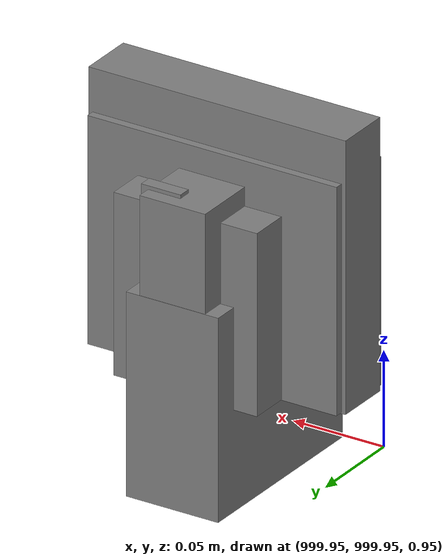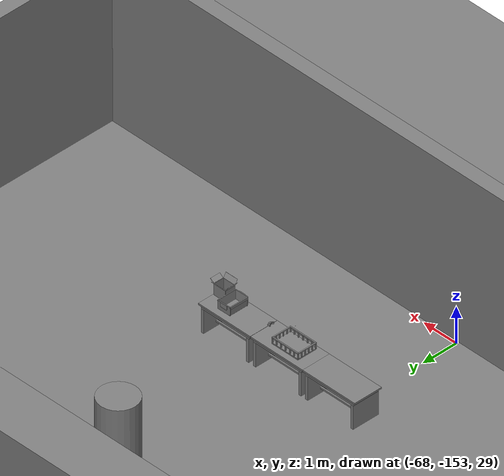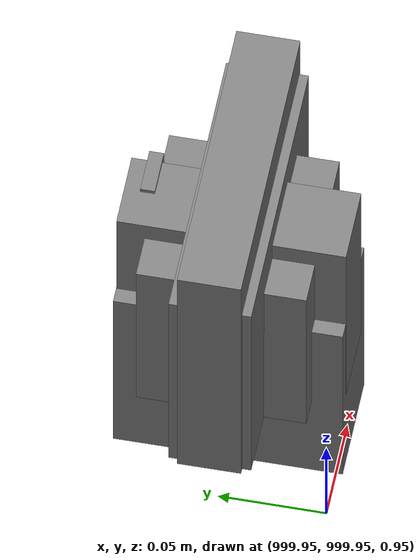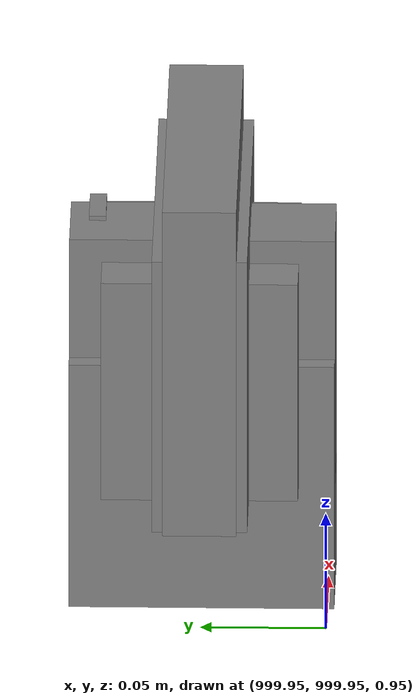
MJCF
<mujoco>
    <option gravity="0.000000000 0.000000000 -9.810000420" timestep="0.0049999999" integrator="implicitfast" density="1.225" viscosity="1.8000001e-05" noslip_iterations="10" iterations="100" sdf_iterations="50">
        <flag multiccd="disable"/>
    </option>
    <size memory="1000M"/>
    <compiler coordinate="local"/>
    <worldbody>
        <light cutoff="30" pos="0 1 1" dir="0 -1 -2"/>
        <light cutoff="30" pos="0 -1 1" dir="0 1 -2"/>
        <body pos="1000.000000000 1000.000000000 1.000000000" euler="0.000000000 0.000000000 180.000000000" name="openloong_gripper_2f85_fix_base_usda_battery_01">
            <geom contype="1" conaffinity="1" density="1000" type="box" material="" rgba="0.500000000 0.500000000 0.500000000 1.000000000" solimp="0.899999976 0.949999988 0.001000000" friction="1.000000000 0.005000000 0.000100000" solref="0.020000000 1.000000000" margin="0" condim="3" group="0" pos="-0.011123657 -0.041940309 0.101691343" quat="1.000000000 0.000000000 0.000000000 0.000000000" size="0.010800000 0.003375000 0.004725000" name="openloong_gripper_2f85_fix_base_usda_geom_753577A5_416F_4700_941E_319EE132C98D"/>
            <geom contype="1" conaffinity="1" density="1000" type="box" material="" rgba="0.500000000 0.500000000 0.500000000 1.000000000" solimp="0.899999976 0.949999988 0.001000000" friction="1.000000000 0.005000000 0.000100000" solref="0.020000000 1.000000000" margin="0" condim="3" group="0" pos="-0.010876465 -0.044247437 0.047066893" quat="0.998702705 -0.050920475 0.000000000 0.000000000" size="0.009450001 0.002700000 0.024975000" name="openloong_gripper_2f85_fix_base_usda_geom_B21AEDEE_768F_432A_9DBB_11A354F662AB"/>
            <geom contype="1" conaffinity="1" density="1000" type="box" material="" rgba="0.500000000 0.500000000 0.500000000 1.000000000" solimp="0.899999976 0.949999988 0.001000000" friction="1.000000000 0.005000000 0.000100000" solref="0.020000000 1.000000000" margin="0" condim="3" group="0" pos="-0.001235962 -0.000659180 0.047381196" quat="1.000000000 0.000000000 0.000000000 0.000000000" size="0.039420001 0.039150000 0.047250003" name="openloong_gripper_2f85_fix_base_usda_geom_B25592F2_3840_4C50_91C6_9BF1960D96E1"/>
            <geom contype="1" conaffinity="1" density="1000" type="box" material="" rgba="0.500000000 0.500000000 0.500000000 1.000000000" solimp="0.899999976 0.949999988 0.001000000" friction="1.000000000 0.005000000 0.000100000" solref="0.020000000 1.000000000" margin="0" condim="3" group="0" pos="-0.010876465 -0.039138794 0.009851727" quat="1.000000000 0.000000000 0.000000000 0.000000000" size="0.009450001 0.010800000 0.013500000" name="openloong_gripper_2f85_fix_base_usda_geom_99442DC1_E3DC_4708_8F26_6F9D21309D9D"/>
            <geom contype="1" conaffinity="1" density="1000" type="box" material="" rgba="0.500000000 0.500000000 0.500000000 1.000000000" solimp="0.899999976 0.949999988 0.001000000" friction="1.000000000 0.005000000 0.000100000" solref="0.020000000 1.000000000" margin="0" condim="3" group="0" pos="-0.010876465 -0.041528322 0.071508206" quat="1.000000000 0.000000000 0.000000000 0.000000000" size="0.009450001 0.002700000 0.027000001" name="openloong_gripper_2f85_fix_base_usda_geom_1D60C14A_D29A_4DF7_AE69_0B76E1293F77"/>
            <freejoint name="openloong_gripper_2f85_fix_base_usda_battery_01_joint"/>
            <site size="0.005000000 0.005000000 0.005000000" rgba="0.500000000 0.500000000 0.500000000 1.000000000" pos="0.000000000 0.000000000 0.000000000" quat="0.999961913 0.008726500 0.000000000 0.000000000" group="0" type="sphere" name="openloong_gripper_2f85_fix_base_usda_battery_01site"/>
        </body>
        <body pos="-65.898696899 -149.384567261 31.170099258" euler="-109.531356812 -39.209148407 34.989997864" mocap="true" name="spotlight6_SpotLight"/>
        <body pos="1000.000000000 1000.000000000 1.000000000" euler="0.000000000 0.000000000 180.000000000" name="openloong_gripper_2f85_fix_base_usda_wifi_box">
            <geom contype="1" conaffinity="1" density="1000" type="box" material="" rgba="0.500000000 0.500000000 0.500000000 1.000000000" solimp="0.899999976 0.949999988 0.001000000" friction="1.000000000 0.005000000 0.000100000" solref="0.020000000 1.000000000" margin="0" condim="3" group="0" pos="0.000000000 0.000000000 0.058978677" quat="0.000000000 0.000000047 0.000000000 1.000000000" size="0.068499997 0.018999999 0.059000000" name="openloong_gripper_2f85_fix_base_usda_geom_C208D5AE_736A_4E08_875C_10C93B48590D"/>
            <freejoint name="openloong_gripper_2f85_fix_base_usda_wifi_box_joint"/>
            <site size="0.005000000 0.005000000 0.005000000" rgba="0.500000000 0.500000000 0.500000000 1.000000000" pos="0.000000000 0.000000000 0.000000000" quat="0.999961913 0.008726500 0.000000000 0.000000000" group="0" type="sphere" name="openloong_gripper_2f85_fix_base_usda_wifi_boxsite"/>
        </body>
        <body pos="1000.000000000 1000.000000000 1.000000000" euler="0.000000000 0.000000000 180.000000000" name="openloong_gripper_2f85_fix_base_usda_cpu_fan">
            <geom contype="1" conaffinity="1" density="1000" type="box" material="" rgba="0.500000000 0.500000000 0.500000000 1.000000000" solimp="0.899999976 0.949999988 0.001000000" friction="1.000000000 0.005000000 0.000100000" solref="0.020000000 1.000000000" margin="0" condim="3" group="0" pos="0.000000000 0.000000000 0.070034981" quat="0.000000000 0.000000000 0.000000000 1.000000000" size="0.070700005 0.014699999 0.070700005" name="openloong_gripper_2f85_fix_base_usda_geom_6A933878_76AA_4035_BBCF_3F9F165F5DDE"/>
            <freejoint name="openloong_gripper_2f85_fix_base_usda_cpu_fan_joint"/>
            <site size="0.005000000 0.005000000 0.005000000" rgba="0.500000000 0.500000000 0.500000000 1.000000000" pos="0.000000000 0.000000000 0.000000000" quat="0.999961913 0.008726535 0.000000000 0.000000000" group="0" type="sphere" name="openloong_gripper_2f85_fix_base_usda_cpu_fancsite"/>
        </body>
        <body pos="1000.000000000 1000.000000000 1.000000000" euler="0.000011953 0.000005123 -179.999984741" name="openloong_gripper_2f85_fix_base_usda_intel_box">
            <geom contype="1" conaffinity="1" density="1000" type="box" material="" rgba="0.500000000 0.500000000 0.500000000 1.000000000" solimp="0.899999976 0.949999988 0.001000000" friction="1.000000000 0.005000000 0.000100000" solref="0.020000000 1.000000000" margin="0" condim="3" group="0" pos="0.000000000 -0.000067139 0.000082284" quat="0.707106709 0.000000225 0.000000253 0.707106650" size="0.052800003 0.025300000 0.052800003" name="openloong_gripper_2f85_fix_base_usda_geom_79319AC9_1FF4_48EA_B8CA_55CECC1679A9"/>
            <freejoint name="openloong_gripper_2f85_fix_base_usda_intel_box_joint"/>
            <site size="0.005000000 0.005000000 0.005000000" rgba="0.500000000 0.500000000 0.500000000 1.000000000" pos="0.000000000 0.000000000 0.000000000" quat="0.999961913 0.008726500 0.000000000 0.000000000" group="0" type="sphere" name="openloong_gripper_2f85_fix_base_usda_intel_boxsite"/>
        </body>
        <body pos="1000.000000000 999.999938965 1.000000000" euler="0.000000000 0.000000000 180.000000000" name="openloong_gripper_2f85_fix_base_usda_intelcore_i5">
            <geom contype="1" conaffinity="1" density="1000" type="box" material="" rgba="0.500000000 0.500000000 0.500000000 1.000000000" solimp="0.899999976 0.949999988 0.001000000" friction="1.000000000 0.005000000 0.000100000" solref="0.020000000 1.000000000" margin="0" condim="3" group="0" pos="0.000000000 0.000000000 0.051722717" quat="0.707106709 0.000000000 0.000000000 -0.707106769" size="0.052800000 0.018080002 0.052800000" name="openloong_gripper_2f85_fix_base_usda_geom_F0C3A167_6338_4801_B83D_8E1ABA421D56"/>
            <freejoint name="openloong_gripper_2f85_fix_base_usda_intelcore_i5_joint"/>
            <site size="0.005000000 0.005000000 0.005000000" rgba="0.500000000 0.500000000 0.500000000 1.000000000" pos="0.000000000 0.000000000 0.000000000" quat="0.999961913 0.008726534 0.000000000 0.000000000" group="0" type="sphere" name="openloong_gripper_2f85_fix_base_usda_intelcore_i5site"/>
        </body>
        <body pos="-66.069046021 -148.845260620 31.164194107" euler="40.181228638 -39.934459686 -23.463087082" mocap="true" name="spotlight2_SpotLight"/>
        <body pos="-65.915443420 -149.489227295 31.165205002" euler="79.135589600 -34.682662964 42.392440796" mocap="true" name="spotlight4_SpotLight"/>
        <body pos="-64.866622925 -149.383972168 30.183746338" euler="89.999984741 89.999946594 0.000000000" name="openloong_gripper_2f85_fix_base_usda_bluebox_01">
            <geom contype="1" conaffinity="1" density="1000" type="box" material="" rgba="0.500000000 0.500000000 0.500000000 1.000000000" solimp="0.899999976 0.949999988 0.001000000" friction="1.000000000 0.005000000 0.000100000" solref="0.020000000 1.000000000" margin="0" condim="3" group="0" pos="0.276580811 0.187225342 0.000068665" quat="0.707106948 0.000077471 0.707106352 0.000077486" size="0.100000001 0.057999998 0.010000000" name="openloong_gripper_2f85_fix_base_usda_geom_014F72E5_AF1A_456B_9FC1_A21103210DE5"/>
            <geom contype="1" conaffinity="1" density="1000" type="box" material="" rgba="0.500000000 0.500000000 0.500000000 1.000000000" solimp="0.899999976 0.949999988 0.001000000" friction="1.000000000 0.005000000 0.000100000" solref="0.020000000 1.000000000" margin="0" condim="3" group="0" pos="0.000000000 0.002883911 0.000000000" quat="0.999999881 0.000000000 0.000000000 0.000000000" size="0.254000008 0.003000000 0.172000006" name="openloong_gripper_2f85_fix_base_usda_geom_2E8C747D_3E48_47E8_BE13_52DE4AE16253"/>
            <geom contype="1" conaffinity="1" density="1000" type="box" material="" rgba="0.500000000 0.500000000 0.500000000 1.000000000" solimp="0.899999976 0.949999988 0.001000000" friction="1.000000000 0.005000000 0.000100000" solref="0.020000000 1.000000000" margin="0" condim="3" group="0" pos="0.000000000 0.124874115 0.173484802" quat="0.999796331 0.020176515 -0.000000015 0.000000030" size="0.259999990 0.119999997 0.007000000" name="openloong_gripper_2f85_fix_base_usda_geom_29ED2801_D3E4_4A2C_9756_49337E57FB5A"/>
            <geom contype="1" conaffinity="1" density="1000" type="box" material="" rgba="0.500000000 0.500000000 0.500000000 1.000000000" solimp="0.899999976 0.949999988 0.001000000" friction="1.000000000 0.005000000 0.000100000" solref="0.020000000 1.000000000" margin="0" condim="3" group="0" pos="0.000000000 0.124874115 -0.173469543" quat="0.999796331 -0.020176545 -0.000000015 0.000000000" size="0.259999990 0.119999997 0.007000000" name="openloong_gripper_2f85_fix_base_usda_geom_01859034_0EE4_43ED_AB9C_F5C57DFF114F"/>
            <geom contype="1" conaffinity="1" density="1000" type="box" material="" rgba="0.500000000 0.500000000 0.500000000 1.000000000" solimp="0.899999976 0.949999988 0.001000000" friction="1.000000000 0.005000000 0.000100000" solref="0.020000000 1.000000000" margin="0" condim="3" group="0" pos="0.000000000 0.214008331 0.188980103" quat="0.999912977 0.013176724 0.000000015 0.000000000" size="0.259999990 0.029999999 0.012500000" name="openloong_gripper_2f85_fix_base_usda_geom_888A62DB_AA06_4DE5_A3FA_9404EB3F12F5"/>
            <geom contype="1" conaffinity="1" density="1000" type="box" material="" rgba="0.500000000 0.500000000 0.500000000 1.000000000" solimp="0.899999976 0.949999988 0.001000000" friction="1.000000000 0.005000000 0.000100000" solref="0.020000000 1.000000000" margin="0" condim="3" group="0" pos="-0.258361816 0.125289917 0.001876831" quat="0.702796936 -0.020792112 0.710783124 0.020769298" size="0.189999998 0.119999997 0.009000000" name="openloong_gripper_2f85_fix_base_usda_geom_E2996985_A03F_4EA9_8AEA_12771B23D2DB"/>
            <geom contype="1" conaffinity="1" density="1000" type="box" material="" rgba="0.500000000 0.500000000 0.500000000 1.000000000" solimp="0.899999976 0.949999988 0.001000000" friction="1.000000000 0.005000000 0.000100000" solref="0.020000000 1.000000000" margin="0" condim="3" group="0" pos="0.000000000 0.214008331 -0.188980103" quat="0.999912977 -0.013176769 0.000000030 0.000000015" size="0.259999990 0.029999999 0.012500000" name="openloong_gripper_2f85_fix_base_usda_geom_C48F2298_65BC_4374_8582_D77582C6648A"/>
            <geom contype="1" conaffinity="1" density="1000" type="box" material="" rgba="0.500000000 0.500000000 0.500000000 1.000000000" solimp="0.899999976 0.949999988 0.001000000" friction="1.000000000 0.005000000 0.000100000" solref="0.020000000 1.000000000" margin="0" condim="3" group="0" pos="-0.276611328 0.187225342 0.000068665" quat="0.707106650 0.000077441 0.707106709 0.000077456" size="0.100000001 0.057999998 0.010000000" name="openloong_gripper_2f85_fix_base_usda_geom_567A5080_D519_4DE1_B3E5_28CF16B7D4EB"/>
            <geom contype="1" conaffinity="1" density="1000" type="box" material="" rgba="0.500000000 0.500000000 0.500000000 1.000000000" solimp="0.899999976 0.949999988 0.001000000" friction="1.000000000 0.005000000 0.000100000" solref="0.020000000 1.000000000" margin="0" condim="3" group="0" pos="0.258331299 0.125289917 0.001876831" quat="0.702851415 0.018856421 0.710823774 -0.019329369" size="0.189999998 0.119999997 0.009000000" name="openloong_gripper_2f85_fix_base_usda_geom_4A6E65E3_3547_47E1_9B9D_691D6B9D9609"/>
            <freejoint name="openloong_gripper_2f85_fix_base_usda_bluebox_01_joint"/>
            <site size="0.005000000 0.005000000 0.005000000" rgba="0.500000000 0.500000000 0.500000000 1.000000000" pos="0.000000000 0.000000000 0.000000000" quat="0.999961913 0.008726534 0.000000000 0.000000000" group="0" type="sphere" name="openloong_gripper_2f85_fix_base_usda_bluebox_01site"/>
        </body>
        <body pos="-64.496299744 -149.491867065 30.235729218" euler="0.000000000 0.000000000 89.999946594" name="openloong_gripper_2f85_fix_base_usda_cardboardbox_01">
            <geom contype="1" conaffinity="1" density="1000" type="box" material="" rgba="0.500000000 0.500000000 0.500000000 1.000000000" solimp="0.899999976 0.949999988 0.001000000" friction="1.000000000 0.005000000 0.000100000" solref="0.020000000 1.000000000" margin="0" condim="3" group="0" pos="-0.003166199 -0.004086494 0.005052090" quat="1.000000000 0.000000000 0.000000000 0.000000000" size="0.142499998 0.177500010 0.005000000" name="openloong_gripper_2f85_fix_base_usda_geom_93E5AF1F_55BA_4409_85D2_498AC5B19A0F"/>
            <geom contype="1" conaffinity="1" density="1000" type="box" material="" rgba="0.500000000 0.500000000 0.500000000 1.000000000" solimp="0.899999976 0.949999988 0.001000000" friction="1.000000000 0.005000000 0.000100000" solref="0.020000000 1.000000000" margin="0" condim="3" group="0" pos="-0.003166199 0.170316696 0.150570869" quat="1.000000000 0.000000000 0.000000000 0.000000000" size="0.142499998 0.005000000 0.149999991" name="openloong_gripper_2f85_fix_base_usda_geom_850119FD_441C_4477_9656_F76944BAB7F6"/>
            <geom contype="1" conaffinity="1" density="1000" type="box" material="" rgba="0.500000000 0.500000000 0.500000000 1.000000000" solimp="0.899999976 0.949999988 0.001000000" friction="1.000000000 0.005000000 0.000100000" solref="0.020000000 1.000000000" margin="0" condim="3" group="0" pos="-0.147399902 -0.005307198 0.150570869" quat="1.000000000 0.000000000 0.000000000 0.000000000" size="0.005000000 0.177500010 0.149999991" name="openloong_gripper_2f85_fix_base_usda_geom_A9EF17D6_02EF_454F_A474_F3C2FAF567A9"/>
            <geom contype="1" conaffinity="1" density="1000" type="box" material="" rgba="0.500000000 0.500000000 0.500000000 1.000000000" solimp="0.899999976 0.949999988 0.001000000" friction="1.000000000 0.005000000 0.000100000" solref="0.020000000 1.000000000" margin="0" condim="3" group="0" pos="0.140275955 -0.005307198 0.150570869" quat="1.000000000 0.000000000 0.000000000 0.000000000" size="0.005000000 0.177500010 0.149999991" name="openloong_gripper_2f85_fix_base_usda_geom_617D4090_D919_4A6F_8567_FD0C64EB8CC1"/>
            <geom contype="1" conaffinity="1" density="1000" type="box" material="" rgba="0.500000000 0.500000000 0.500000000 1.000000000" solimp="0.899999976 0.949999988 0.001000000" friction="1.000000000 0.005000000 0.000100000" solref="0.020000000 1.000000000" margin="0" condim="3" group="0" pos="-0.003166199 -0.181550980 0.150570869" quat="1.000000000 0.000000000 0.000000000 0.000000000" size="0.142499998 0.005000000 0.149999991" name="openloong_gripper_2f85_fix_base_usda_geom_FACBF19A_9C9A_4E94_80C9_70ACB22C1B28"/>
            <freejoint name="openloong_gripper_2f85_fix_base_usda_cardboardbox_01_joint"/>
            <site size="0.005000000 0.005000000 0.005000000" rgba="0.500000000 0.500000000 0.500000000 1.000000000" pos="0.000000000 0.000000000 0.000000000" quat="0.999961913 0.008726535 0.000000000 0.000000000" group="0" type="sphere" name="openloong_gripper_2f85_fix_base_usda_site_32AA1CDC_64B7_4DDB_BC6D_78EDA91DE2B3"/>
            <body pos="0.139160156 -0.004048347 0.301930904" euler="-179.999954224 49.383502960 179.999954224" name="openloong_gripper_2f85_fix_base_usda_A1_006">
                <geom contype="1" conaffinity="1" density="1000" type="box" material="" rgba="0.500000000 0.500000000 0.500000000 1.000000000" solimp="0.899999976 0.949999988 0.001000000" friction="1.000000000 0.005000000 0.000100000" solref="0.020000000 1.000000000" margin="0" condim="3" group="0" pos="-0.071587563 0.000009537 0.001745224" quat="0.999999881 0.000000000 0.000000000 0.000000000" size="0.071249999 0.179999992 0.002500000" name="openloong_gripper_2f85_fix_base_usda_geom_CDA5D719_20B5_47E9_B016_C9CDC5D50BF9"/>
                <joint armature="0" stiffness="0.07" damping="0.0099999998" axis="0.000000 1.000000 0.000000" type="hinge" name="openloong_gripper_2f85_fix_base_usda_A1_006"/>
            </body>
            <body pos="-0.145902634 -0.004086494 0.301938057" euler="-180.000000000 -60.000011444 -180.000000000" name="openloong_gripper_2f85_fix_base_usda_A2_006">
                <geom contype="1" conaffinity="1" density="1000" type="box" material="" rgba="0.500000000 0.500000000 0.500000000 1.000000000" solimp="0.899999976 0.949999988 0.001000000" friction="1.000000000 0.005000000 0.000100000" solref="0.020000000 1.000000000" margin="0" condim="3" group="0" pos="0.071268082 0.000009537 0.002717972" quat="0.000002921 0.000000000 -0.000000030 0.999999881" size="0.071249999 0.179999992 0.002500000" name="openloong_gripper_2f85_fix_base_usda_geom_1F79E522_7353_4AF8_85CC_4BCC31736C3D"/>
                <joint armature="0" stiffness="0.07" damping="0.0099999998" axis="0.000000 1.000000 0.000000" type="hinge" name="openloong_gripper_2f85_fix_base_usda_A2_006"/>
            </body>
            <body pos="-0.003385544 0.175991058 0.301930904" euler="-125.858116150 -0.000004561 0.000002331" name="openloong_gripper_2f85_fix_base_usda_B2_006">
                <geom contype="1" conaffinity="1" density="1000" type="box" material="" rgba="0.500000000 0.500000000 0.500000000 1.000000000" solimp="0.899999976 0.949999988 0.001000000" friction="1.000000000 0.005000000 0.000100000" solref="0.020000000 1.000000000" margin="0" condim="3" group="0" pos="0.000009537 -0.070939064 -0.002470016" quat="0.999614120 0.027776197 -0.000000015 0.000000030" size="0.137500003 0.064999998 0.005000000" name="openloong_gripper_2f85_fix_base_usda_geom_5E01F830_B31A_4BCD_82DD_CF5665574249"/>
                <joint armature="0" stiffness="0.07" damping="0.0099999998" axis="1.000000 0.000000 0.000000" type="hinge" name="openloong_gripper_2f85_fix_base_usda_B2_006"/>
            </body>
            <body pos="-0.003385544 -0.184140205 0.301938057" euler="147.805557251 0.000000000 0.000000000" name="openloong_gripper_2f85_fix_base_usda_B1_006">
                <geom contype="1" conaffinity="1" density="1000" type="box" material="" rgba="0.500000000 0.500000000 0.500000000 1.000000000" solimp="0.899999976 0.949999988 0.001000000" friction="1.000000000 0.005000000 0.000100000" solref="0.020000000 1.000000000" margin="0" condim="3" group="0" pos="-0.000028610 0.070202351 -0.002703667" quat="0.999614179 -0.027776167 0.000000000 0.000000000" size="0.137500003 0.064999998 0.005000000" name="openloong_gripper_2f85_fix_base_usda_geom_6C8AAA1D_D854_47DB_9129_23B35EB615CC"/>
                <joint armature="0" stiffness="0.07" damping="0.0099999998" axis="1.000000 0.000000 0.000000" type="hinge" name="openloong_gripper_2f85_fix_base_usda_B1_006"/>
            </body>
        </body>
        <body pos="-65.882858276 -149.481979370 30.229999542" euler="-64.487716675 0.000000000 0.000000000" name="openloong_gripper_2f85_fix_base_usda_Barcode">
            <geom contype="1" conaffinity="1" density="1000" type="box" material="" rgba="0.500000000 0.500000000 0.500000000 1.000000000" solimp="0.899999976 0.949999988 0.001000000" friction="1.000000000 0.005000000 0.000100000" solref="0.020000000 1.000000000" margin="0" condim="3" group="0" pos="0.000000000 0.013038635 0.001419067" quat="0.000000000 0.000000000 0.000000000 1.000000119" size="0.034000002 0.010000000 0.017999999" name="openloong_gripper_2f85_fix_base_usda_geom_84DECABF_F9ED_46BC_BC3D_7CBECB881A11"/>
            <geom contype="1" conaffinity="1" density="1000" type="box" material="" rgba="0.500000000 0.500000000 0.500000000 1.000000000" solimp="0.899999976 0.949999988 0.001000000" friction="1.000000000 0.005000000 0.000100000" solref="0.020000000 1.000000000" margin="0" condim="3" group="0" pos="0.000000000 -0.035301208 -0.007095337" quat="0.000000000 0.000000000 -0.043619365 0.999048233" size="0.028999999 0.010000000 0.020000000" name="openloong_gripper_2f85_fix_base_usda_geom_B423D280_B968_4546_9835_616649BEBF99"/>
            <geom contype="1" conaffinity="1" density="1000" type="box" material="" rgba="0.500000000 0.500000000 0.500000000 1.000000000" solimp="0.899999976 0.949999988 0.001000000" friction="1.000000000 0.005000000 0.000100000" solref="0.020000000 1.000000000" margin="0" condim="3" group="0" pos="0.000000000 -0.043411255 -0.011749268" quat="0.922262907 0.386563420 0.000000000 0.000000000" size="0.026000001 0.010000000 0.020000000" name="openloong_gripper_2f85_fix_base_usda_geom_8446544C_19A7_42CC_9707_F281932922F4"/>
            <geom contype="1" conaffinity="1" density="1000" type="box" material="" rgba="0.500000000 0.500000000 0.500000000 1.000000000" solimp="0.899999976 0.949999988 0.001000000" friction="1.000000000 0.005000000 0.000100000" solref="0.020000000 1.000000000" margin="0" condim="3" group="0" pos="0.000000000 -0.016967773 -0.031860352" quat="0.000000000 0.000000000 0.000000000 1.000000119" size="0.008000000 0.010000000 0.013000000" name="openloong_gripper_2f85_fix_base_usda_geom_F0F3E967_6703_4C7A_9758_6269E489E6E2"/>
            <geom contype="1" conaffinity="1" density="1000" type="box" material="" rgba="0.500000000 0.500000000 0.500000000 1.000000000" solimp="0.899999976 0.949999988 0.001000000" friction="1.000000000 0.005000000 0.000100000" solref="0.020000000 1.000000000" margin="0" condim="3" group="0" pos="0.000000000 -0.001869202 0.000312805" quat="0.953716993 0.300705761 0.000000000 0.000000000" size="0.032000002 0.010000000 0.018999999" name="openloong_gripper_2f85_fix_base_usda_geom_426CA4D7_9753_4A0F_B828_09BA92C2F45A"/>
            <geom contype="1" conaffinity="1" density="1000" type="box" material="" rgba="0.500000000 0.500000000 0.500000000 1.000000000" solimp="0.899999976 0.949999988 0.001000000" friction="1.000000000 0.005000000 0.000100000" solref="0.020000000 1.000000000" margin="0" condim="3" group="0" pos="0.000000000 -0.019531250 -0.003173828" quat="0.953716993 0.300705761 0.000000000 0.000000000" size="0.030999999 0.010000000 0.020000000" name="openloong_gripper_2f85_fix_base_usda_geom_89830428_2089_4327_A92A_0475A9571C96"/>
            <geom contype="1" conaffinity="1" density="1000" type="box" material="" rgba="0.500000000 0.500000000 0.500000000 1.000000000" solimp="0.899999976 0.949999988 0.001000000" friction="1.000000000 0.005000000 0.000100000" solref="0.020000000 1.000000000" margin="0" condim="3" group="0" pos="0.000000000 -0.035301208 -0.007095337" quat="0.953716993 0.300705761 0.000000000 0.000000000" size="0.028999999 0.010000000 0.020000000" name="openloong_gripper_2f85_fix_base_usda_geom_45F2FDDD_FDED_4341_B270_23FD9D0C4FCF"/>
            <geom contype="1" conaffinity="1" density="1000" type="box" material="" rgba="0.500000000 0.500000000 0.500000000 1.000000000" solimp="0.899999976 0.949999988 0.001000000" friction="1.000000000 0.005000000 0.000100000" solref="0.020000000 1.000000000" margin="0" condim="3" group="0" pos="0.000000000 -0.042617798 -0.071121216" quat="0.000000000 0.000000000 0.000000000 1.000000119" size="0.013000000 0.021000000 0.059999999" name="openloong_gripper_2f85_fix_base_usda_geom_2AFE11E0_CF7F_4817_B702_06F9AFBCF4A0"/>
            <freejoint name="openloong_gripper_2f85_fix_base_usda_Barcode_joint"/>
            <site size="0.005000000 0.005000000 0.005000000" rgba="0.500000000 0.500000000 0.500000000 1.000000000" pos="0.000000000 0.000000000 0.000000000" quat="1.000000000 0.000000000 0.000000000 0.000000000" group="0" type="sphere" name="openloong_gripper_2f85_fix_base_usda_Barcode_site"/>
        </body>
        <body pos="-66.745018005 -149.392349243 30.184000015" euler="0.000000000 0.000000000 89.999946594" name="[22332964515634]_Basket_01">
            <geom contype="1" conaffinity="1" density="1000" type="box" material="" rgba="0.500000000 0.500000000 0.500000000 1.000000000" solimp="0.899999976 0.949999988 0.001000000" friction="1.000000000 0.005000000 0.000100000" solref="0.020000000 1.000000000" margin="0" condim="3" group="0" pos="-0.052425385 0.389207840 0.089787483" quat="0.707107008 0.000000000 0.000000000 0.707106411" size="0.014249999 0.014249999 0.059999999" name="[22332964515634]_geom_7D0F1A53_9175_4E94_9B89_449144EF0C20"/>
            <geom contype="1" conaffinity="1" density="1000" type="box" material="" rgba="0.500000000 0.500000000 0.500000000 1.000000000" solimp="0.899999976 0.949999988 0.001000000" friction="1.000000000 0.005000000 0.000100000" solref="0.020000000 1.000000000" margin="0" condim="3" group="0" pos="0.264015198 -0.133043289 0.089787483" quat="0.707107008 0.000000000 0.000000000 0.707106411" size="0.014249999 0.014249999 0.059999999" name="[22332964515634]_geom_EE0D75DD_547B_4B37_9089_AB79147970EA"/>
            <geom contype="1" conaffinity="1" density="1000" type="box" material="" rgba="0.500000000 0.500000000 0.500000000 1.000000000" solimp="0.899999976 0.949999988 0.001000000" friction="1.000000000 0.005000000 0.000100000" solref="0.020000000 1.000000000" margin="0" condim="3" group="0" pos="-0.264015198 -0.265548706 0.089793205" quat="0.707107008 0.000000000 0.000000000 0.707106411" size="0.014249999 0.014249999 0.059999999" name="[22332964515634]_geom_25785F08_9C12_40D5_A93F_39343755E193"/>
            <geom contype="1" conaffinity="1" density="1000" type="box" material="" rgba="0.500000000 0.500000000 0.500000000 1.000000000" solimp="0.899999976 0.949999988 0.001000000" friction="1.000000000 0.005000000 0.000100000" solref="0.020000000 1.000000000" margin="0" condim="3" group="0" pos="-0.160263062 -0.389322281 0.089793205" quat="0.707107008 0.000000000 0.000000000 0.707106411" size="0.014249999 0.014249999 0.059999999" name="[22332964515634]_geom_78EEBD01_BCE3_44E7_A1BF_165066BDF975"/>
            <geom contype="1" conaffinity="1" density="1000" type="box" material="" rgba="0.500000000 0.500000000 0.500000000 1.000000000" solimp="0.899999976 0.949999988 0.001000000" friction="1.000000000 0.005000000 0.000100000" solref="0.020000000 1.000000000" margin="0" condim="3" group="0" pos="0.162265778 -0.389322281 0.089787483" quat="0.707107008 0.000000000 0.000000000 0.707106411" size="0.014249999 0.014249999 0.059999999" name="[22332964515634]_geom_82AEF735_75B8_405B_825D_B57DD27AA6AA"/>
            <geom contype="1" conaffinity="1" density="1000" type="box" material="" rgba="0.500000000 0.500000000 0.500000000 1.000000000" solimp="0.899999976 0.949999988 0.001000000" friction="1.000000000 0.005000000 0.000100000" solref="0.020000000 1.000000000" margin="0" condim="3" group="0" pos="0.264015198 0.389207840 0.089787483" quat="0.707107008 0.000000000 0.000000000 0.707106411" size="0.014249999 0.014249999 0.059999999" name="[22332964515634]_geom_56494182_29B7_441B_9862_71D67B88299A"/>
            <geom contype="1" conaffinity="1" density="1000" type="box" material="" rgba="0.500000000 0.500000000 0.500000000 1.000000000" solimp="0.899999976 0.949999988 0.001000000" friction="1.000000000 0.005000000 0.000100000" solref="0.020000000 1.000000000" margin="0" condim="3" group="0" pos="-0.264015198 -0.133043289 0.089793205" quat="0.707107008 0.000000000 0.000000000 0.707106411" size="0.014249999 0.014249999 0.059999999" name="[22332964515634]_geom_3569694B_DE60_4595_816D_13A9B5F80BAA"/>
            <geom contype="1" conaffinity="1" density="1000" type="box" material="" rgba="0.500000000 0.500000000 0.500000000 1.000000000" solimp="0.899999976 0.949999988 0.001000000" friction="1.000000000 0.005000000 0.000100000" solref="0.020000000 1.000000000" margin="0" condim="3" group="0" pos="-0.264026642 0.269256592 0.089793205" quat="0.707107008 0.000000000 0.000000000 0.707106411" size="0.014249999 0.014249999 0.059999999" name="[22332964515634]_geom_A3C2A687_10EA_498C_8570_AA5E83515E2B"/>
            <geom contype="1" conaffinity="1" density="1000" type="box" material="" rgba="0.500000000 0.500000000 0.500000000 1.000000000" solimp="0.899999976 0.949999988 0.001000000" friction="1.000000000 0.005000000 0.000100000" solref="0.020000000 1.000000000" margin="0" condim="3" group="0" pos="0.054462433 0.389207840 0.089787483" quat="0.707107008 0.000000000 0.000000000 0.707106411" size="0.014249999 0.014249999 0.059999999" name="[22332964515634]_geom_D46CBE57_028B_4AE1_BFFF_12D874C7A6D0"/>
            <geom contype="1" conaffinity="1" density="1000" type="box" material="" rgba="0.500000000 0.500000000 0.500000000 1.000000000" solimp="0.899999976 0.949999988 0.001000000" friction="1.000000000 0.005000000 0.000100000" solref="0.020000000 1.000000000" margin="0" condim="3" group="0" pos="0.054462433 -0.389322281 0.089787483" quat="0.707107008 0.000000000 0.000000000 0.707106411" size="0.014249999 0.014249999 0.059999999" name="[22332964515634]_geom_A69107F5_B9E6_431F_A768_C9B60B9A379C"/>
            <geom contype="1" conaffinity="1" density="1000" type="box" material="" rgba="0.500000000 0.500000000 0.500000000 1.000000000" solimp="0.899999976 0.949999988 0.001000000" friction="1.000000000 0.005000000 0.000100000" solref="0.020000000 1.000000000" margin="0" condim="3" group="0" pos="0.264015198 0.269256592 0.089793205" quat="0.707107008 0.000000000 0.000000000 0.707106411" size="0.014249999 0.014249999 0.059999999" name="[22332964515634]_geom_1BC68E9E_9A18_4250_A36C_1BE2F8C42AE9"/>
            <geom contype="1" conaffinity="1" density="1000" type="box" material="" rgba="0.500000000 0.500000000 0.500000000 1.000000000" solimp="0.899999976 0.949999988 0.001000000" friction="1.000000000 0.005000000 0.000100000" solref="0.020000000 1.000000000" margin="0" condim="3" group="0" pos="0.264015198 -0.389322281 0.089787483" quat="0.707107008 0.000000000 0.000000000 0.707106411" size="0.014249999 0.014249999 0.059999999" name="[22332964515634]_geom_111497D7_8A58_4B6D_A273_E741045FC6AC"/>
            <geom contype="1" conaffinity="1" density="1000" type="box" material="" rgba="0.500000000 0.500000000 0.500000000 1.000000000" solimp="0.899999976 0.949999988 0.001000000" friction="1.000000000 0.005000000 0.000100000" solref="0.020000000 1.000000000" margin="0" condim="3" group="0" pos="0.000000000 0.000000000 0.015998840" quat="0.707107008 0.000000000 0.000000000 0.707106411" size="0.403499991 0.279000014 0.015750000" name="[22332964515634]_geom_FFD52C60_9498_4C96_832F_2CEE54B7AB22"/>
            <geom contype="1" conaffinity="1" density="1000" type="box" material="" rgba="0.500000000 0.500000000 0.500000000 1.000000000" solimp="0.899999976 0.949999988 0.001000000" friction="1.000000000 0.005000000 0.000100000" solref="0.020000000 1.000000000" margin="0" condim="3" group="0" pos="0.000000000 -0.389476776 0.163619041" quat="0.707107008 0.000000000 0.000000000 0.707106411" size="0.015000000 0.277500004 0.015750000" name="[22332964515634]_geom_17CABCF0_AA3E_456E_90A2_4D2F8820E1A3"/>
            <geom contype="1" conaffinity="1" density="1000" type="box" material="" rgba="0.500000000 0.500000000 0.500000000 1.000000000" solimp="0.899999976 0.949999988 0.001000000" friction="1.000000000 0.005000000 0.000100000" solref="0.020000000 1.000000000" margin="0" condim="3" group="0" pos="0.162265778 0.389207840 0.089787483" quat="0.707107008 0.000000000 0.000000000 0.707106411" size="0.014249999 0.014249999 0.059999999" name="[22332964515634]_geom_5D135DBF_B871_445E_BC06_06264926EA12"/>
            <geom contype="1" conaffinity="1" density="1000" type="box" material="" rgba="0.500000000 0.500000000 0.500000000 1.000000000" solimp="0.899999976 0.949999988 0.001000000" friction="1.000000000 0.005000000 0.000100000" solref="0.020000000 1.000000000" margin="0" condim="3" group="0" pos="0.000000000 0.389471054 0.163619041" quat="0.707107008 0.000000000 0.000000000 0.707106411" size="0.015000000 0.277500004 0.015750000" name="[22332964515634]_geom_E6B4AE7A_9ADC_4FB8_807A_32255BB01594"/>
            <geom contype="1" conaffinity="1" density="1000" type="box" material="" rgba="0.500000000 0.500000000 0.500000000 1.000000000" solimp="0.899999976 0.949999988 0.001000000" friction="1.000000000 0.005000000 0.000100000" solref="0.020000000 1.000000000" margin="0" condim="3" group="0" pos="-0.263511658 0.000000000 0.163619041" quat="0.707107008 0.000000000 0.000000000 0.707106411" size="0.403499991 0.015000000 0.015750000" name="[22332964515634]_geom_EE33F6EC_0B20_479A_A6B6_4046704CC6B5"/>
            <geom contype="1" conaffinity="1" density="1000" type="box" material="" rgba="0.500000000 0.500000000 0.500000000 1.000000000" solimp="0.899999976 0.949999988 0.001000000" friction="1.000000000 0.005000000 0.000100000" solref="0.020000000 1.000000000" margin="0" condim="3" group="0" pos="-0.264015198 0.141334534 0.089793205" quat="0.707107008 0.000000000 0.000000000 0.707106411" size="0.014249999 0.014249999 0.059999999" name="[22332964515634]_geom_98C5CCCF_9A44_4F03_AB11_7FB9ACE11815"/>
            <geom contype="1" conaffinity="1" density="1000" type="box" material="" rgba="0.500000000 0.500000000 0.500000000 1.000000000" solimp="0.899999976 0.949999988 0.001000000" friction="1.000000000 0.005000000 0.000100000" solref="0.020000000 1.000000000" margin="0" condim="3" group="0" pos="0.264015198 -0.265548706 0.089787483" quat="0.707107008 0.000000000 0.000000000 0.707106411" size="0.014249999 0.014249999 0.059999999" name="[22332964515634]_geom_E5F09265_B114_44EA_861A_6ABCE8FDE08A"/>
            <geom contype="1" conaffinity="1" density="1000" type="box" material="" rgba="0.500000000 0.500000000 0.500000000 1.000000000" solimp="0.899999976 0.949999988 0.001000000" friction="1.000000000 0.005000000 0.000100000" solref="0.020000000 1.000000000" margin="0" condim="3" group="0" pos="-0.160263062 0.389207840 0.089787483" quat="0.707107008 0.000000000 0.000000000 0.707106411" size="0.014249999 0.014249999 0.059999999" name="[22332964515634]_geom_8E035F0B_0C9D_446B_85CB_D63F8DB4147A"/>
            <geom contype="1" conaffinity="1" density="1000" type="box" material="" rgba="0.500000000 0.500000000 0.500000000 1.000000000" solimp="0.899999976 0.949999988 0.001000000" friction="1.000000000 0.005000000 0.000100000" solref="0.020000000 1.000000000" margin="0" condim="3" group="0" pos="-0.052425385 -0.389322281 0.089787483" quat="0.707107008 0.000000000 0.000000000 0.707106411" size="0.014249999 0.014249999 0.059999999" name="[22332964515634]_geom_A1245034_E588_434E_8401_ACB95A58295C"/>
            <geom contype="1" conaffinity="1" density="1000" type="box" material="" rgba="0.500000000 0.500000000 0.500000000 1.000000000" solimp="0.899999976 0.949999988 0.001000000" friction="1.000000000 0.005000000 0.000100000" solref="0.020000000 1.000000000" margin="0" condim="3" group="0" pos="-0.264026642 -0.389322281 0.089793205" quat="0.707107008 0.000000000 0.000000000 0.707106411" size="0.014249999 0.014249999 0.059999999" name="[22332964515634]_geom_AF31CFA4_C161_4E62_8406_A83774ADA593"/>
            <geom contype="1" conaffinity="1" density="1000" type="box" material="" rgba="0.500000000 0.500000000 0.500000000 1.000000000" solimp="0.899999976 0.949999988 0.001000000" friction="1.000000000 0.005000000 0.000100000" solref="0.020000000 1.000000000" margin="0" condim="3" group="0" pos="0.264015198 0.141334534 0.089787483" quat="0.707107008 0.000000000 0.000000000 0.707106411" size="0.014249999 0.014249999 0.059999999" name="[22332964515634]_geom_D2DBB401_7D19_4F2B_93FE_054AE3B376A3"/>
            <geom contype="1" conaffinity="1" density="1000" type="box" material="" rgba="0.500000000 0.500000000 0.500000000 1.000000000" solimp="0.899999976 0.949999988 0.001000000" friction="1.000000000 0.005000000 0.000100000" solref="0.020000000 1.000000000" margin="0" condim="3" group="0" pos="-0.264015198 0.389207840 0.089793205" quat="0.707107008 0.000000000 0.000000000 0.707106411" size="0.014249999 0.014249999 0.059999999" name="[22332964515634]_geom_2C91D123_469F_416C_90AE_CD35A1FB27FA"/>
            <geom contype="1" conaffinity="1" density="1000" type="box" material="" rgba="0.500000000 0.500000000 0.500000000 1.000000000" solimp="0.899999976 0.949999988 0.001000000" friction="1.000000000 0.005000000 0.000100000" solref="0.020000000 1.000000000" margin="0" condim="3" group="0" pos="0.264015198 0.004480362 0.089787483" quat="0.707107008 0.000000000 0.000000000 0.707106411" size="0.014249999 0.014249999 0.059999999" name="[22332964515634]_geom_E775C7D5_4BE3_4698_B731_342B568907DF"/>
            <geom contype="1" conaffinity="1" density="1000" type="box" material="" rgba="0.500000000 0.500000000 0.500000000 1.000000000" solimp="0.899999976 0.949999988 0.001000000" friction="1.000000000 0.005000000 0.000100000" solref="0.020000000 1.000000000" margin="0" condim="3" group="0" pos="0.263694763 -0.000011444 0.163619041" quat="0.707107008 0.000000000 0.000000000 0.707106411" size="0.403499991 0.015000000 0.015750000" name="[22332964515634]_geom_39B860FD_729B_48D0_8220_4567B55CE2D6"/>
            <geom contype="1" conaffinity="1" density="1000" type="box" material="" rgba="0.500000000 0.500000000 0.500000000 1.000000000" solimp="0.899999976 0.949999988 0.001000000" friction="1.000000000 0.005000000 0.000100000" solref="0.020000000 1.000000000" margin="0" condim="3" group="0" pos="-0.264015198 0.004480362 0.089793205" quat="0.707107008 0.000000000 0.000000000 0.707106411" size="0.014249999 0.014249999 0.059999999" name="[22332964515634]_geom_20720D33_1224_42C8_AEF6_D654A8ACDBB4"/>
            <freejoint name="[22332964515634]_joint_A1BD2A54_B17A_4B71_AF71_12C77B643BE0"/>
        </body>
        <body pos="0.000000000 0.000000000 0.000000000" euler="0.000000000 0.000000000 0.000000000" name="Static Objects_Static Objects">
            <geom contype="1" conaffinity="1" density="1000" type="box" material="" rgba="0.500000000 0.500000000 0.500000000 1.000000000" solimp="0.899999976 0.949999988 0.001000000" friction="1.000000000 0.005000000 0.000100000" solref="0.020000000 1.000000000" margin="0" condim="3" group="0" pos="-67.544113159 -149.365814209 29.727830887" quat="0.500000417 0.499999970 0.499999553 0.499999970" size="0.381000012 0.319999993 0.041000001" name="Static Objects_geom_DB9972B0_D603_4297_B5B7_EE2AB90C29D1"/>
            <geom contype="1" conaffinity="1" density="1000" type="box" material="" rgba="0.500000000 0.500000000 0.500000000 1.000000000" solimp="0.899999976 0.949999988 0.001000000" friction="1.000000000 0.005000000 0.000100000" solref="0.020000000 1.000000000" margin="0" condim="3" group="0" pos="-68.239501953 -149.365814209 30.086868286" quat="0.500000417 0.499999970 0.499999553 0.499999970" size="0.370999992 0.039500002 0.745000005" name="Static Objects_geom_C2587B1A_E8F4_41E1_A135_A0251D29D30C"/>
            <geom contype="1" conaffinity="1" density="1000" type="box" material="" rgba="0.500000000 0.500000000 0.500000000 1.000000000" solimp="0.899999976 0.949999988 0.001000000" friction="1.000000000 0.005000000 0.000100000" solref="0.020000000 1.000000000" margin="0" condim="3" group="0" pos="-68.239501953 -149.365814209 30.147235870" quat="0.500000417 0.499999970 0.499999553 0.499999970" size="0.400000006 0.022000000 0.800000012" name="Static Objects_geom_43B314DF_1E62_41EE_8021_89F7A0C3CB09"/>
            <geom contype="1" conaffinity="1" density="1000" type="box" material="" rgba="0.500000000 0.500000000 0.500000000 1.000000000" solimp="0.899999976 0.949999988 0.001000000" friction="1.000000000 0.005000000 0.000100000" solref="0.020000000 1.000000000" margin="0" condim="3" group="0" pos="-68.934890747 -149.365814209 29.727830887" quat="0.500000417 0.499999970 0.499999553 0.499999970" size="0.381000012 0.319999993 0.041000001" name="Static Objects_geom_80E97D96_A1AB_411E_8882_AFBAD546DB37"/>
            <geom contype="1" conaffinity="1" density="1000" type="box" material="" rgba="0.500000000 0.500000000 0.500000000 1.000000000" solimp="0.899999976 0.949999988 0.001000000" friction="1.000000000 0.005000000 0.000100000" solref="0.020000000 1.000000000" margin="0" condim="3" group="0" pos="-68.239501953 -149.365814209 29.561563492" quat="0.500000417 0.499999970 0.499999553 0.499999970" size="0.020000000 0.022000000 0.660000026" name="Static Objects_geom_0F4FE92C_2961_4C4F_9F9F_25D8FF707A37"/>
            <geom contype="1" conaffinity="1" density="1000" type="box" material="" rgba="0.500000000 0.500000000 0.500000000 1.000000000" solimp="0.899999976 0.949999988 0.001000000" friction="1.000000000 0.005000000 0.000100000" solref="0.020000000 1.000000000" margin="0" condim="3" group="0" pos="-65.945671082 -149.365814209 29.727830887" quat="0.500000417 0.499999970 0.499999553 0.499999970" size="0.381000012 0.319999993 0.041000001" name="Static Objects_geom_C2ED67A8_B1F4_4EBD_8B48_23B9B8CC5CDC"/>
            <geom contype="1" conaffinity="1" density="1000" type="box" material="" rgba="0.500000000 0.500000000 0.500000000 1.000000000" solimp="0.899999976 0.949999988 0.001000000" friction="1.000000000 0.005000000 0.000100000" solref="0.020000000 1.000000000" margin="0" condim="3" group="0" pos="-66.641059875 -149.365814209 30.086868286" quat="0.500000417 0.499999970 0.499999553 0.499999970" size="0.370999992 0.039500002 0.745000005" name="Static Objects_geom_C365A49E_15BC_438A_887D_E64B755B7E67"/>
            <geom contype="1" conaffinity="1" density="1000" type="box" material="" rgba="0.500000000 0.500000000 0.500000000 1.000000000" solimp="0.899999976 0.949999988 0.001000000" friction="1.000000000 0.005000000 0.000100000" solref="0.020000000 1.000000000" margin="0" condim="3" group="0" pos="-66.641059875 -149.365814209 30.147235870" quat="0.500000417 0.499999970 0.499999553 0.499999970" size="0.400000006 0.022000000 0.800000012" name="Static Objects_geom_FBE33B04_B2EB_409F_A366_CA89D9FDA7DA"/>
            <geom contype="1" conaffinity="1" density="1000" type="box" material="" rgba="0.500000000 0.500000000 0.500000000 1.000000000" solimp="0.899999976 0.949999988 0.001000000" friction="1.000000000 0.005000000 0.000100000" solref="0.020000000 1.000000000" margin="0" condim="3" group="0" pos="-67.336448669 -149.365814209 29.727830887" quat="0.500000417 0.499999970 0.499999553 0.499999970" size="0.381000012 0.319999993 0.041000001" name="Static Objects_geom_B26CA8C5_7A7D_4B76_B7DB_ACA2E359AEB3"/>
            <geom contype="1" conaffinity="1" density="1000" type="box" material="" rgba="0.500000000 0.500000000 0.500000000 1.000000000" solimp="0.899999976 0.949999988 0.001000000" friction="1.000000000 0.005000000 0.000100000" solref="0.020000000 1.000000000" margin="0" condim="3" group="0" pos="-66.641059875 -149.365814209 29.561563492" quat="0.500000417 0.499999970 0.499999553 0.499999970" size="0.020000000 0.022000000 0.660000026" name="Static Objects_geom_B21430B2_B66C_4EE2_9171_9E78AAC36E4D"/>
            <geom contype="1" conaffinity="1" density="1000" type="box" material="" rgba="0.500000000 0.500000000 0.500000000 1.000000000" solimp="0.899999976 0.949999988 0.001000000" friction="1.000000000 0.005000000 0.000100000" solref="0.020000000 1.000000000" margin="0" condim="3" group="0" pos="-64.338577271 -149.365814209 29.727830887" quat="0.500000417 0.499999970 0.499999553 0.499999970" size="0.381000012 0.319999993 0.041000001" name="Static Objects_geom_4A65B4A7_A37D_4A46_8BCC_420F44C00A0A"/>
            <geom contype="1" conaffinity="1" density="1000" type="box" material="" rgba="0.500000000 0.500000000 0.500000000 1.000000000" solimp="0.899999976 0.949999988 0.001000000" friction="1.000000000 0.005000000 0.000100000" solref="0.020000000 1.000000000" margin="0" condim="3" group="0" pos="-65.033966064 -149.365814209 30.086868286" quat="0.500000417 0.499999970 0.499999553 0.499999970" size="0.370999992 0.039500002 0.745000005" name="Static Objects_geom_6771708F_78F7_4DE8_A456_EFBB5FB1CF2F"/>
            <geom contype="1" conaffinity="1" density="1000" type="box" material="" rgba="0.500000000 0.500000000 0.500000000 1.000000000" solimp="0.899999976 0.949999988 0.001000000" friction="1.000000000 0.005000000 0.000100000" solref="0.020000000 1.000000000" margin="0" condim="3" group="0" pos="-65.033966064 -149.365814209 30.147235870" quat="0.500000417 0.499999970 0.499999553 0.499999970" size="0.400000006 0.022000000 0.800000012" name="Static Objects_geom_DB669E5A_5BC0_49E3_A48F_3C39FFA9FBCE"/>
            <geom contype="1" conaffinity="1" density="1000" type="box" material="" rgba="0.500000000 0.500000000 0.500000000 1.000000000" solimp="0.899999976 0.949999988 0.001000000" friction="1.000000000 0.005000000 0.000100000" solref="0.020000000 1.000000000" margin="0" condim="3" group="0" pos="-65.729354858 -149.365814209 29.727830887" quat="0.500000417 0.499999970 0.499999553 0.499999970" size="0.381000012 0.319999993 0.041000001" name="Static Objects_geom_A63136B3_1557_4FF5_83EB_F3C5432340ED"/>
            <geom contype="1" conaffinity="1" density="1000" type="box" material="" rgba="0.500000000 0.500000000 0.500000000 1.000000000" solimp="0.899999976 0.949999988 0.001000000" friction="1.000000000 0.005000000 0.000100000" solref="0.020000000 1.000000000" margin="0" condim="3" group="0" pos="-65.033966064 -149.365814209 29.561563492" quat="0.500000417 0.499999970 0.499999553 0.499999970" size="0.020000000 0.022000000 0.660000026" name="Static Objects_geom_8417F30C_FB17_42E5_894D_D02EE71E1D26"/>
            <geom contype="1" conaffinity="1" density="1000" type="box" material="" rgba="0.500000000 0.500000000 0.500000000 1.000000000" solimp="0.899999976 0.949999988 0.001000000" friction="1.000000000 0.005000000 0.000100000" solref="0.020000000 1.000000000" margin="0" condim="3" group="0" pos="-61.754566193 -137.853729248 33.906845093" quat="0.707107067 0.000000000 0.000000000 0.707106471" size="0.759999990 0.759999990 4.500000000" name="Static Objects_geom_C0277A97_695B_4628_9F5E_470BB0EA14CA"/>
            <geom contype="1" conaffinity="1" density="1000" type="box" material="" rgba="0.500000000 0.500000000 0.500000000 1.000000000" solimp="0.899999976 0.949999988 0.001000000" friction="1.000000000 0.005000000 0.000100000" solref="0.020000000 1.000000000" margin="0" condim="3" group="0" pos="-57.511135101 -144.927108765 31.707921982" quat="1.000000000 0.000000000 0.000000000 0.000000000" size="0.200000003 8.000000000 2.299999952" name="Static Objects_geom_38C77C66_BA0D_48AF_B641_62DC77967D56"/>
            <geom contype="1" conaffinity="1" density="1000" type="box" material="" rgba="0.500000000 0.500000000 0.500000000 1.000000000" solimp="0.899999976 0.949999988 0.001000000" friction="1.000000000 0.005000000 0.000100000" solref="0.020000000 1.000000000" margin="0" condim="3" group="0" pos="-80.517646790 -157.574050903 31.688196182" quat="0.707107067 0.000000000 0.000000000 0.707106471" size="0.600000024 0.600000024 2.299999952" name="Static Objects_geom_B46CF4D4_1279_419F_ABAB_180835E0ED25"/>
            <geom contype="1" conaffinity="1" density="1000" type="box" material="" rgba="0.500000000 0.500000000 0.500000000 1.000000000" solimp="0.899999976 0.949999988 0.001000000" friction="1.000000000 0.005000000 0.000100000" solref="0.020000000 1.000000000" margin="0" condim="3" group="0" pos="-80.711044312 -147.414932251 31.666158676" quat="1.000000000 0.000000000 0.000000000 0.000000000" size="0.200000003 10.000000000 2.299999952" name="Static Objects_geom_88CB78F7_8243_4DD2_9591_C4A7741E9796"/>
            <geom contype="1" conaffinity="1" density="1000" type="box" material="" rgba="0.500000000 0.500000000 0.500000000 1.000000000" solimp="0.899999976 0.949999988 0.001000000" friction="1.000000000 0.005000000 0.000100000" solref="0.020000000 1.000000000" margin="0" condim="3" group="0" pos="-57.687217712 -137.434692383 31.688196182" quat="0.707107067 0.000000000 0.000000000 0.707106471" size="0.600000024 0.600000024 2.299999952" name="Static Objects_geom_5A36F85F_0256_45DB_8210_DD5373D09636"/>
            <geom contype="1" conaffinity="1" density="1000" type="box" material="" rgba="0.500000000 0.500000000 0.500000000 1.000000000" solimp="0.899999976 0.949999988 0.001000000" friction="1.000000000 0.005000000 0.000100000" solref="0.020000000 1.000000000" margin="0" condim="3" group="0" pos="-69.537033081 -140.263229370 31.714921951" quat="0.707107067 0.000000000 0.000000000 0.707106471" size="0.759999990 4.500000000 2.299999952" name="Static Objects_geom_D33C89AA_587A_4D08_98DD_16BD8335E772"/>
            <geom contype="1" conaffinity="1" density="1000" type="box" material="" rgba="0.500000000 0.500000000 0.500000000 1.000000000" solimp="0.899999976 0.949999988 0.001000000" friction="1.000000000 0.005000000 0.000100000" solref="0.020000000 1.000000000" margin="0" condim="3" group="0" pos="-80.073638916 -137.853713989 33.906845093" quat="0.707107067 0.000000000 0.000000000 0.707106471" size="0.759999990 0.759999990 4.500000000" name="Static Objects_geom_BEF212D6_B8F6_4187_AC46_562782147F61"/>
            <geom contype="1" conaffinity="1" density="1000" type="box" material="" rgba="0.500000000 0.500000000 0.500000000 1.000000000" solimp="0.899999976 0.949999988 0.001000000" friction="1.000000000 0.005000000 0.000100000" solref="0.020000000 1.000000000" margin="0" condim="3" group="0" pos="-73.406707764 -155.734664917 31.707921982" quat="1.000000000 0.000000000 0.000000000 0.000000000" size="0.200000003 3.000000000 2.299999952" name="Static Objects_geom_F1B34E50_1FCC_4DC7_B43D_F393ED68BDBC"/>
            <geom contype="1" conaffinity="1" density="1000" type="box" material="" rgba="0.500000000 0.500000000 0.500000000 1.000000000" solimp="0.899999976 0.949999988 0.001000000" friction="1.000000000 0.005000000 0.000100000" solref="0.020000000 1.000000000" margin="0" condim="3" group="0" pos="-68.497543335 -137.448257446 31.707921982" quat="0.707107067 0.000000000 0.000000000 0.707106471" size="0.200000003 14.000000000 2.299999952" name="Static Objects_geom_04066764_3025_4F97_BF66_16EFBEE3D1E4"/>
            <geom contype="1" conaffinity="1" density="1000" type="cylinder" material="" rgba="0.500000000 0.500000000 0.500000000 1.000000000" solimp="0.899999976 0.949999988 0.001000000" friction="1.000000000 0.005000000 0.000100000" solref="0.020000000 1.000000000" margin="0" condim="3" group="0" pos="-68.868522644 -142.134506226 31.711090088" quat="0.707107067 0.000000000 0.000000000 0.707106471" size="0.509999990 2.299999952 1.000000000" name="Static Objects_geom_1B87C753_DC4A_4EC7_972B_C0BD0DFD4E17"/>
            <geom contype="1" conaffinity="1" density="1000" type="plane" material="" rgba="0.500000000 0.500000000 0.500000000 1.000000000" solimp="0.899999976 0.949999988 0.001000000" friction="1.000000000 0.005000000 0.000100000" solref="0.020000000 1.000000000" margin="0" condim="3" group="0" pos="-72.873703003 -147.131927490 29.409669876" quat="1.000000000 0.000000000 0.000000000 0.000000000" size="18.000000000 14.000000000 1.000000000" name="Static Objects_geom_6F66B7B1_98E7_42EE_9C1D_CB16E7C5E68D"/>
            <geom contype="1" conaffinity="1" density="1000" type="box" material="" rgba="0.500000000 0.500000000 0.500000000 1.000000000" solimp="0.899999976 0.949999988 0.001000000" friction="1.000000000 0.005000000 0.000100000" solref="0.020000000 1.000000000" margin="0" condim="3" group="0" pos="-79.943580627 -157.782272339 31.707921982" quat="0.707107067 0.000000000 0.000000000 0.707106471" size="0.200000003 7.000000000 2.299999952" name="Static Objects_geom_1CD01BC1_FDC2_4174_A278_95E4410D8C7C"/>
            <geom contype="1" conaffinity="1" density="1000" type="box" material="" rgba="0.500000000 0.500000000 0.500000000 1.000000000" solimp="0.899999976 0.949999988 0.001000000" friction="1.000000000 0.005000000 0.000100000" solref="0.020000000 1.000000000" margin="0" condim="3" group="0" pos="-65.421028137 -152.903442383 31.707921982" quat="0.707107067 0.000000000 0.000000000 0.707106471" size="0.200000003 7.800000191 2.299999952" name="Static Objects_geom_164E78D5_6975_428F_AA45_52EE3220CAAB"/>
            <geom contype="1" conaffinity="1" density="1000" type="box" material="" rgba="0.500000000 0.500000000 0.500000000 1.000000000" solimp="0.899999976 0.949999988 0.001000000" friction="1.000000000 0.005000000 0.000100000" solref="0.020000000 1.000000000" margin="0" condim="3" group="0" pos="-74.776908875 -149.964416504 31.688196182" quat="1.000000000 0.000000000 0.000000000 0.000000000" size="0.600000024 0.409999996 2.299999952" name="Static Objects_geom_A93BCBEA_D25D_4A3A_8D71_6839137F2D93"/>
            <geom contype="1" conaffinity="1" density="1000" type="cylinder" material="" rgba="0.500000000 0.500000000 0.500000000 1.000000000" solimp="0.899999976 0.949999988 0.001000000" friction="1.000000000 0.005000000 0.000100000" solref="0.020000000 1.000000000" margin="0" condim="3" group="0" pos="-60.161884308 -142.134506226 31.711090088" quat="0.707107067 0.000000000 0.000000000 0.707106471" size="0.509999990 2.299999952 1.000000000" name="Static Objects_geom_47E9C525_6347_4B41_BDDB_20A068BB3E24"/>
            <geom contype="1" conaffinity="1" density="1000" type="cylinder" material="" rgba="0.500000000 0.500000000 0.500000000 1.000000000" solimp="0.899999976 0.949999988 0.001000000" friction="1.000000000 0.005000000 0.000100000" solref="0.020000000 1.000000000" margin="0" condim="3" group="0" pos="-75.382453918 -149.963455200 31.711090088" quat="0.707107067 0.000000000 0.000000000 0.707106471" size="0.409999996 2.299999952 1.000000000" name="Static Objects_geom_1235D689_F92F_409A_8ED6_476EDA050BA5"/>
            <geom contype="1" conaffinity="1" density="1000" type="cylinder" material="" rgba="0.500000000 0.500000000 0.500000000 1.000000000" solimp="0.899999976 0.949999988 0.001000000" friction="1.000000000 0.005000000 0.000100000" solref="0.020000000 1.000000000" margin="0" condim="3" group="0" pos="-74.154960632 -149.963455200 31.711090088" quat="0.707107067 0.000000000 0.000000000 0.707106471" size="0.409999996 2.299999952 1.000000000" name="Static Objects_geom_83FC6E30_CD03_4D59_A33D_C762C9CAB70C"/>
            <geom contype="1" conaffinity="1" density="1000" type="cylinder" material="" rgba="0.500000000 0.500000000 0.500000000 1.000000000" solimp="0.899999976 0.949999988 0.001000000" friction="1.000000000 0.005000000 0.000100000" solref="0.020000000 1.000000000" margin="0" condim="3" group="0" pos="-77.566612244 -142.134506226 31.711090088" quat="0.707107067 0.000000000 0.000000000 0.707106471" size="0.509999990 2.299999952 1.000000000" name="Static Objects_geom_70FD730E_DD3F_434F_9B08_C67A9741BF32"/>
        </body>
        <body pos="-66.291030884 -149.869689941 29.018842697" euler="0.000000000 0.000000000 89.999946594" mocap="true" name="openloong_gripper_2f85_fix_base_usda_leftHandMocap"/>
        <body pos="-66.291030884 -149.869689941 29.018842697" euler="0.000000000 0.000000000 89.999946594" mocap="true" name="openloong_gripper_2f85_fix_base_usda_rightHandMocap"/>
        <body pos="-66.291030884 -149.869689941 30.218843460" euler="0.000000000 0.000000000 89.999946594" name="openloong_gripper_2f85_fix_base_usda_base_link">
            <geom contype="1" conaffinity="1" density="1000" type="mesh" material="" rgba="0.783999979 0.783999979 0.783999979 1.000000000" solimp="0.899999976 0.949999988 0.001000000" friction="1.000000000 0.005000000 0.000100000" solref="0.020000000 1.000000000" margin="0" condim="3" group="3" mesh="base_link" pos="0.000000000 0.000000000 0.000000000" quat="1.000000000 0.000000000 0.000000000 0.000000000" size="1.000000000 1.000000000 1.000000000" name="openloong_gripper_2f85_fix_base_usda__geom_7_3A626549_F511_4DCD_A92F_7083F7EC9CE8"/>
            <site size="0.005000000 0.005000000 0.005000000" rgba="0.500000000 0.500000000 0.500000000 1.000000000" pos="0.000000000 0.000000000 0.000000000" quat="1.000000000 0.000000000 0.000000000 0.000000000" group="0" type="sphere" name="openloong_gripper_2f85_fix_base_usda_imu"/>
            <inertial mass="22.447001" pos="-0.005664100 -0.001336700 0.238289997" diaginertia="0.374352545 0.277180195 0.220617250" quat="0.999247074 0.035235517 -0.015086859 0.006023135"/>
            <body pos="0.000000000 0.000000000 0.299997330" euler="0.000000000 0.000000000 0.000000000" name="openloong_gripper_2f85_fix_base_usda_dummy_body">
                <geom contype="1" conaffinity="1" density="1000" type="sphere" material="" rgba="0.783999979 0.783999979 0.783999979 1.000000000" solimp="0.899999976 0.949999988 0.001000000" friction="1.000000000 0.005000000 0.000100000" solref="0.020000000 1.000000000" margin="0" condim="3" group="3" pos="0.000000000 0.000000000 0.000000000" quat="1.000000000 0.000000000 0.000000000 0.000000000" size="0.010000000 0.000000000 0.000000000" name="openloong_gripper_2f85_fix_base_usda__geom_8_88FBBEB0_B4F2_4BFA_8999_45BDB8BAB1CD"/>
                <joint armature="0.0099999998" stiffness="0" damping="0.1" axis="0.000000 0.000000 1.000000" type="hinge" name="openloong_gripper_2f85_fix_base_usda_dummy_joint"/>
                <site size="0.010000000 0.005000000 0.005000000" rgba="0.500000000 0.500000000 0.500000000 1.000000000" pos="0.000000000 0.000000000 0.000000000" quat="1.000000000 0.000000000 0.000000000 0.000000000" group="3" type="sphere" name="openloong_gripper_2f85_fix_base_usda_dummy_site"/>
            </body>
            <body pos="0.009002686 0.000000000 0.406400681" euler="0.000000000 0.000000000 0.000000000" name="openloong_gripper_2f85_fix_base_usda_Link_head_yaw">
                <geom contype="1" conaffinity="1" density="1000" type="mesh" material="" rgba="0.783999979 0.783999979 0.783999979 1.000000000" solimp="0.899999976 0.949999988 0.001000000" friction="1.000000000 0.005000000 0.000100000" solref="0.020000000 1.000000000" margin="0" condim="3" group="3" mesh="Link_head_yaw" pos="0.000000000 0.000000000 0.000000000" quat="1.000000000 0.000000000 0.000000000 0.000000000" size="1.000000000 1.000000000 1.000000000" name="openloong_gripper_2f85_fix_base_usda__geom_10_3C211ABE_2B62_4D28_AF76_2542FE0FDED6"/>
                <inertial mass="0.84249002" pos="0.000000000 -0.002081400 0.044801001" diaginertia="0.000700588 0.000629000 0.000553812" quat="0.706933022 -0.015675601 0.015677100 0.706933022"/>
                <body pos="0.000000000 -0.034599304 0.048500061" euler="0.000000000 0.000000000 0.000000000" name="openloong_gripper_2f85_fix_base_usda_Link_head_pitch">
                    <geom contype="1" conaffinity="1" density="1000" type="mesh" material="" rgba="0.783999979 0.783999979 0.783999979 1.000000000" solimp="0.899999976 0.949999988 0.001000000" friction="1.000000000 0.005000000 0.000100000" solref="0.020000000 1.000000000" margin="0" condim="3" group="3" mesh="Link_head_pitch" pos="0.000000000 0.000000000 0.000000000" quat="1.000000000 0.000000000 0.000000000 0.000000000" size="1.000000000 1.000000000 1.000000000" name="openloong_gripper_2f85_fix_base_usda__geom_12_F3F91088_0DB1_46F6_8B0D_646291AFF364"/>
                    <inertial mass="1.3943" pos="0.020569000 0.033004001 0.125000000" diaginertia="0.006381400 0.006289940 0.004481460" quat="0.973390222 0.008406822 0.228157058 0.019624906"/>
                    <body pos="0.000000000 0.029998779 0.000000000" euler="0.000000000 0.000000000 0.000000000" name="openloong_gripper_2f85_fix_base_usda_neck_center_body">
                        <site size="0.010000000 0.005000000 0.005000000" rgba="0.500000000 0.500000000 0.500000000 1.000000000" pos="0.000000000 0.000000000 0.000000000" quat="1.000000000 0.000000000 0.000000000 0.000000000" group="3" type="sphere" name="openloong_gripper_2f85_fix_base_usda_neck_center_site"/>
                        <body pos="0.020004272 0.000000000 0.149999619" euler="-0.000002229 39.998176575 -90.000205994" name="openloong_gripper_2f85_fix_base_usda_camera_head">
                            <site size="0.010000000 0.005000000 0.005000000" rgba="0.500000000 0.500000000 0.500000000 1.000000000" pos="0.000000000 0.000000000 0.000000000" quat="1.000000000 0.000000000 0.000000000 0.000000000" group="3" type="sphere" name="openloong_gripper_2f85_fix_base_usda_camera_head_site"/>
                        </body>
                    </body>
                </body>
            </body>
            <body pos="0.003997803 -0.161598206 0.392200470" euler="0.000000000 0.000000000 0.000000000" name="openloong_gripper_2f85_fix_base_usda_Link_arm_r_01">
                <geom contype="1" conaffinity="1" density="1000" type="mesh" material="" rgba="0.783999979 0.783999979 0.783999979 1.000000000" solimp="0.899999976 0.949999988 0.001000000" friction="1.000000000 0.005000000 0.000100000" solref="0.020000000 1.000000000" margin="0" condim="3" group="3" mesh="Link_arm_r_01" pos="0.000000000 0.000000000 0.000000000" quat="1.000000000 0.000000000 0.000000000 0.000000000" size="1.000000000 1.000000000 1.000000000" name="openloong_gripper_2f85_fix_base_usda__geom_14_BB1CCD43_134D_4229_8FDB_460DEF54408F"/>
                <joint armature="0.0099999998" stiffness="0" damping="1" axis="0.000000 -1.000000 0.000000" limited="true" range="-170.000015259 170.000015259" type="hinge" name="openloong_gripper_2f85_fix_base_usda_J_arm_r_01"/>
                <inertial mass="0.75641" pos="0.004494600 -0.038293999 -0.000001874" diaginertia="0.000842990 0.000803050 0.000587120" quat="-0.000163502 0.707098067 0.000812463 0.707115054"/>
                <body pos="-0.041992188 -0.041000366 0.000000000" euler="0.000000000 0.000000000 0.000000000" name="openloong_gripper_2f85_fix_base_usda_Link_arm_r_02">
                    <geom contype="1" conaffinity="1" density="1000" type="mesh" material="" rgba="0.783999979 0.783999979 0.783999979 1.000000000" solimp="0.899999976 0.949999988 0.001000000" friction="1.000000000 0.005000000 0.000100000" solref="0.020000000 1.000000000" margin="0" condim="3" group="3" mesh="Link_arm_r_02" pos="0.000000000 0.000000000 0.000000000" quat="1.000000000 0.000000000 0.000000000 0.000000000" size="1.000000000 1.000000000 1.000000000" name="openloong_gripper_2f85_fix_base_usda__geom_16_BDA016F5_CB01_4DEF_800F_7CBEF876BA59"/>
                    <joint armature="0.0099999998" stiffness="0" damping="1" axis="-1.000000 0.000000 0.000000" limited="true" range="-105.000244141 105.000244141" type="hinge" name="openloong_gripper_2f85_fix_base_usda_J_arm_r_02"/>
                    <inertial mass="0.98500001" pos="0.041999999 -0.067430697 0.000000000" diaginertia="0.002262690 0.001730990 0.001154020" quat="0.500000000 0.500000000 -0.500000000 0.500000000"/>
                    <body pos="0.041992188 -0.122596741 0.000000000" euler="0.000000000 0.000000000 0.000000000" name="openloong_gripper_2f85_fix_base_usda_Link_arm_r_03">
                        <geom contype="1" conaffinity="1" density="1000" type="mesh" material="" rgba="0.783999979 0.783999979 0.783999979 1.000000000" solimp="0.899999976 0.949999988 0.001000000" friction="1.000000000 0.005000000 0.000100000" solref="0.020000000 1.000000000" margin="0" condim="3" group="3" mesh="Link_arm_r_03" pos="0.000000000 0.000000000 0.000000000" quat="1.000000000 0.000000000 0.000000000 0.000000000" size="1.000000000 1.000000000 1.000000000" name="openloong_gripper_2f85_fix_base_usda__geom_18_7859F7F5_CAF6_4D70_9147_9712CBFEA784"/>
                        <joint armature="0.0099999998" stiffness="0" damping="1" axis="0.000000 -1.000000 0.000000" limited="true" range="-170.000015259 170.000015259" type="hinge" name="openloong_gripper_2f85_fix_base_usda_J_arm_r_03"/>
                        <inertial mass="0.95899999" pos="-0.001413580 -0.164663002 0.020757901" diaginertia="0.002101340 0.002064590 0.000754802" quat="0.560480952 0.454391927 -0.443732947 0.531497955"/>
                        <body pos="0.035293579 -0.177406311 0.023998260" euler="0.000000000 0.000000000 0.000000000" name="openloong_gripper_2f85_fix_base_usda_Link_arm_r_04">
                            <geom contype="1" conaffinity="1" density="1000" type="mesh" material="" rgba="0.783999979 0.783999979 0.783999979 1.000000000" solimp="0.899999976 0.949999988 0.001000000" friction="1.000000000 0.005000000 0.000100000" solref="0.020000000 1.000000000" margin="0" condim="3" group="3" mesh="Link_arm_r_04" pos="0.000000000 0.000000000 0.000000000" quat="1.000000000 0.000000000 0.000000000 0.000000000" size="1.000000000 1.000000000 1.000000000" name="openloong_gripper_2f85_fix_base_usda__geom_20_DD78E5A7_4DBD_4B00_8DEB_857934D2CD4B"/>
                            <joint armature="0.0099999998" stiffness="0" damping="1" axis="-1.000000 0.000000 0.000000" limited="true" range="0.000000000 170.000015259" type="hinge" name="openloong_gripper_2f85_fix_base_usda_J_arm_r_04"/>
                            <inertial mass="0.60000002" pos="-0.038727000 -0.060766999 -0.021003000" diaginertia="0.001092610 0.000712422 0.000645102" quat="0.327701002 0.632602990 -0.467366993 0.523443997"/>
                            <body pos="-0.035293579 -0.103492737 -0.023998260" euler="0.000000000 0.000000000 0.000000000" name="openloong_gripper_2f85_fix_base_usda_Link_arm_r_05">
                                <geom contype="1" conaffinity="1" density="1000" type="mesh" material="" rgba="0.783999979 0.783999979 0.783999979 1.000000000" solimp="0.899999976 0.949999988 0.001000000" friction="1.000000000 0.005000000 0.000100000" solref="0.020000000 1.000000000" margin="0" condim="3" group="3" mesh="Link_arm_r_05" pos="0.000000000 0.000000000 0.000000000" quat="1.000000000 0.000000000 0.000000000 0.000000000" size="1.000000000 1.000000000 1.000000000" name="openloong_gripper_2f85_fix_base_usda__geom_22_AB0C43C7_2CB0_4F8B_983E_16CD8ECCD6D1"/>
                                <joint armature="0.0099999998" stiffness="0" damping="1" axis="0.000000 -1.000000 0.000000" limited="true" range="-170.000015259 170.000015259" type="hinge" name="openloong_gripper_2f85_fix_base_usda_J_arm_r_05"/>
                                <inertial mass="0.68976003" pos="0.000032712 -0.068658002 -0.000111780" diaginertia="0.002522510 0.002411100 0.000448695" quat="0.707660973 0.706543028 -0.002603360 0.002470550"/>
                                <body pos="-0.026489258 -0.196502686 0.000000000" euler="0.000000000 0.000000000 0.000000000" name="openloong_gripper_2f85_fix_base_usda_Link_arm_r_06">
                                    <geom contype="1" conaffinity="1" density="1000" type="mesh" material="" rgba="0.783999979 0.783999979 0.783999979 1.000000000" solimp="0.899999976 0.949999988 0.001000000" friction="1.000000000 0.005000000 0.000100000" solref="0.020000000 1.000000000" margin="0" condim="3" group="3" mesh="Link_arm_r_06" pos="0.000000000 0.000000000 0.000000000" quat="1.000000000 0.000000000 0.000000000 0.000000000" size="1.000000000 1.000000000 1.000000000" name="openloong_gripper_2f85_fix_base_usda__geom_24_6289F56A_4CF7_4FCC_9AB1_FB52DF08BBE6"/>
                                    <joint armature="0.0099999998" stiffness="0" damping="1" axis="1.000000 0.000000 0.000000" limited="true" range="-105.000244141 105.000244141" type="hinge" name="openloong_gripper_2f85_fix_base_usda_J_arm_r_06"/>
                                    <inertial mass="0.28" pos="0.026078001 -0.000000896 0.001663700" diaginertia="0.000156930 0.000145601 0.000104979" quat="0.707080841 0.001851080 0.001883810 0.707127810"/>
                                    <body pos="0.026489258 0.000000000 0.031799316" euler="0.000000000 0.000000000 0.000000000" name="openloong_gripper_2f85_fix_base_usda_Link_arm_r_07">
                                        <geom contype="1" conaffinity="1" density="1000" type="mesh" material="" rgba="0.783999979 0.783999979 0.783999979 1.000000000" solimp="0.899999976 0.949999988 0.001000000" friction="1.000000000 0.005000000 0.000100000" solref="0.020000000 1.000000000" margin="0" condim="3" group="3" mesh="Link_arm_r_07" pos="0.000000000 0.000000000 0.000000000" quat="1.000000000 0.000000000 0.000000000 0.000000000" size="1.000000000 1.000000000 1.000000000" name="openloong_gripper_2f85_fix_base_usda__geom_26_C91A8EC1_5D2B_47BD_A925_C59676A31897"/>
                                        <joint armature="0.0099999998" stiffness="0" damping="1" axis="0.000000 0.000000 1.000000" limited="true" range="-60.000133514 60.000133514" type="hinge" name="openloong_gripper_2f85_fix_base_usda_J_arm_r_07"/>
                                        <inertial mass="0.61353999" pos="-0.007859000 -0.158170000 -0.027736001" diaginertia="0.003037610 0.002570910 0.000729379" quat="0.427542925 0.443532884 -0.553093910 0.560867906"/>
                                        <body pos="0.000000000 0.286994934 -0.270000458" euler="150.000350952 -0.000001649 -0.000000442" name="openloong_gripper_2f85_fix_base_usda_camera_wrist_r">
                                            <site size="0.010000000 0.005000000 0.005000000" rgba="0.500000000 0.500000000 0.500000000 1.000000000" pos="0.000000000 0.000000000 0.000000000" quat="1.000000000 0.000000000 0.000000000 0.000000000" group="3" type="sphere" name="openloong_gripper_2f85_fix_base_usda_camera_wrist_r_site"/>
                                        </body>
                                        <body pos="0.000000000 -0.220008850 -0.033002853" euler="0.000000000 0.000000000 179.999969482" name="openloong_gripper_2f85_fix_base_usda_ee_center_body_r">
                                            <site size="0.010000000 0.005000000 0.005000000" rgba="0.500000000 0.500000000 0.500000000 1.000000000" pos="0.000000000 0.000000000 0.000000000" quat="1.000000000 0.000000000 0.000000000 0.000000000" group="3" type="sphere" name="openloong_gripper_2f85_fix_base_usda_ee_center_site_r"/>
                                        </body>
                                        <body pos="0.000000000 -0.066001892 -0.031000137" euler="89.999984741 0.000000000 180.000000000" name="openloong_gripper_2f85_fix_base_usda_zbr_base_link">
                                            <geom contype="1" conaffinity="1" density="1000" type="mesh" material="" rgba="0.783999979 0.783999979 0.783999979 1.000000000" solimp="0.899999976 0.949999988 0.001000000" friction="1.000000000 0.005000000 0.000100000" solref="0.020000000 1.000000000" margin="0" condim="3" group="3" mesh="base" pos="0.000000000 0.000003815 -0.000007629" quat="1.000000000 0.000000000 0.000000000 0.000000000" size="1.000000238 1.000000238 1.000000238" name="openloong_gripper_2f85_fix_base_usda__geom_30_EBCEA142_0F81_4184_8079_C6457AB16C12"/>
                                            <inertial mass="0.77744102" pos="0.000000000 -0.000027039 0.035467502" diaginertia="0.000260285 0.000225381 0.000152708" quat="0.999998808 -0.001528488 0.000000000 0.000000000"/>
                                            <body pos="-0.030609138 0.004745484 0.065696731" euler="-89.999984741 -0.000000000 0.000000000" name="openloong_gripper_2f85_fix_base_usda_r_left_driver">
                                                <geom contype="1" conaffinity="1" density="1000" type="mesh" material="" rgba="0.783999979 0.783999979 0.783999979 1.000000000" solimp="0.899999976 0.949999988 0.001000000" friction="1.000000000 0.005000000 0.000100000" solref="0.020000000 1.000000000" margin="0" condim="3" group="3" mesh="driver" pos="0.030609138 0.054901138 -0.004699708" quat="0.707106829 0.707106709 0.000000000 -0.000000000" size="1.000000238 1.000000238 1.000000238" name="openloong_gripper_2f85_fix_base_usda__geom_32_A36FBE70_615A_4917_BF90_665899470123"/>
                                                <joint armature="0.0049999999" stiffness="0" damping="0.1" axis="0.000000 0.000000 1.000000" limited="true" range="0.000000000 51.566200256" type="hinge" name="openloong_gripper_2f85_fix_base_usda_r_left_driver_joint"/>
                                                <inertial mass="0.0089956298" pos="0.000000000 0.017754700 0.001073140" diaginertia="0.000001724 0.000001609 0.000000322" quat="0.681301236 0.732003212 0.000000000 0.000000000"/>
                                                <body pos="-0.031402595 0.004524232 -0.010200503" euler="0.000000000 0.000000000 180.000000000" name="openloong_gripper_2f85_fix_base_usda_r_left_coupler">
                                                    <geom contype="1" conaffinity="1" density="1000" type="mesh" material="" rgba="0.783999979 0.783999979 0.783999979 1.000000000" solimp="0.899999976 0.949999988 0.001000000" friction="1.000000000 0.005000000 0.000100000" solref="0.020000000 1.000000000" margin="0" condim="3" group="3" mesh="coupler" pos="-0.062011734 -0.050354015 0.005500795" quat="0.707106829 -0.707106709 0.000000000 -0.000000000" size="1.000000238 1.000000238 1.000000238" name="openloong_gripper_2f85_fix_base_usda__geom_34_4B9111F0_C1A3_4B35_B23C_4F5209BC1D74"/>
                                                    <inertial mass="0.0140974" pos="0.000000000 0.003012090 0.023217499" diaginertia="0.000004162 0.000003522 0.000000888" quat="0.705635548 -0.045590367 0.045590367 0.705635548"/>
                                                </body>
                                            </body>
                                            <body pos="-0.012695315 -0.012001040 0.072212234" euler="-89.999984741 -0.000000000 0.000000000" name="openloong_gripper_2f85_fix_base_usda_r_left_spring_link">
                                                <geom contype="1" conaffinity="1" density="1000" type="mesh" material="" rgba="0.783999979 0.783999979 0.783999979 1.000000000" solimp="0.899999976 0.949999988 0.001000000" friction="1.000000000 0.005000000 0.000100000" solref="0.020000000 1.000000000" margin="0" condim="3" group="3" mesh="spring_link" pos="0.012695315 0.061416641 0.012050631" quat="0.707106829 0.707106709 0.000000000 -0.000000000" size="1.000000238 1.000000238 1.000000238" name="openloong_gripper_2f85_fix_base_usda__geom_36_74DCED61_436D_42C9_AE59_44E0AC414782"/>
                                                <joint armature="0.001" stiffness="0.050000001" damping="0.00125" axis="0.000000 0.000000 1.000000" limited="true" range="-17.000000000 51.566200256" type="hinge" name="openloong_gripper_2f85_fix_base_usda_r_left_spring_link_joint"/>
                                                <inertial mass="0.0221642" pos="-0.000000009 0.018162400 0.021265799" diaginertia="0.000008969 0.000006717 0.000002639" quat="0.663403213 -0.244737089 0.244737089 0.663403213"/>
                                                <body pos="-0.038208015 -0.042503368 0.002950669" euler="180.000000000 0.000000000 -0.002185660" name="openloong_gripper_2f85_fix_base_usda_r_left_follower">
                                                    <geom contype="1" conaffinity="1" density="1000" type="mesh" material="" rgba="0.783999979 0.783999979 0.783999979 1.000000000" solimp="0.899999976 0.949999988 0.001000000" friction="1.000000000 0.005000000 0.000100000" solref="0.020000000 1.000000000" margin="0" condim="3" group="3" mesh="tongue" pos="0.050918590 -0.103920005 -0.009099962" quat="0.707106829 -0.707106709 0.000000030 0.000000030" size="1.000000238 1.000000238 1.000000238" name="openloong_gripper_2f85_fix_base_usda__geom_40_4D7042B1_EA27_46ED_9869_5C5A88B0DCB6"/>
                                                    <geom contype="1" conaffinity="1" density="1000" type="mesh" material="" rgba="0.783999979 0.783999979 0.783999979 1.000000000" solimp="0.899999976 0.949999988 0.001000000" friction="1.000000000 0.005000000 0.000100000" solref="0.020000000 1.000000000" margin="0" condim="3" group="3" mesh="follower" pos="0.050918590 -0.103920005 -0.009099962" quat="0.707106829 -0.707106709 0.000000030 0.000000030" size="1.000000238 1.000000238 1.000000238" name="openloong_gripper_2f85_fix_base_usda__geom_39_7A6D0801_1DC9_440F_80EA_E065982211CE"/>
                                                    <joint armature="0.001" stiffness="0" damping="0.1" axis="0.000000 0.000000 1.000000" limited="true" range="-49.999961853 51.566200256" type="hinge" name="openloong_gripper_2f85_fix_base_usda_r_left_follower"/>
                                                    <inertial mass="0.0125222" pos="0.000000000 -0.011046000 0.012478600" diaginertia="0.000002674 0.000002456 0.000000602" quat="0.986436546 0.164143041 0.000000000 0.000000000"/>
                                                    <body pos="-0.037765510 -0.103912376 -0.009099962" euler="-89.999984741 0.000000000 0.000004829" name="openloong_gripper_2f85_fix_base_usda_r_left_pad">
                                                        <geom contype="1" conaffinity="1" density="1000" type="box" material="" rgba="0.550000012 0.550000012 0.550000012 1.000000000" solimp="0.949999988 0.990000010 0.001000000" friction="0.699999988 0.005000000 0.000100000" solref="0.020000000 1.000000000" margin="0" condim="3" group="3" mass="1e-06" pos="0.043243419 0.000003815 0.119995147" quat="0.999999881 0.000000000 0.000000000 0.000000000" size="0.002000001 0.011000003 0.009375002" name="openloong_gripper_2f85_fix_base_usda_r_left_pad1_8746940E_EE47_4BF8_95E2_8E3CD354E88D"/>
                                                        <geom contype="1" conaffinity="1" density="1000" type="box" material="" rgba="0.449999988 0.449999988 0.449999988 1.000000000" solimp="0.949999988 0.990000010 0.001000000" friction="0.600000024 0.005000000 0.000100000" solref="0.020000000 1.000000000" margin="0" condim="3" group="3" mass="1e-06" pos="0.043243419 0.000003815 0.138748199" quat="0.999999881 0.000000000 0.000000000 0.000000000" size="0.002000001 0.011000003 0.009375002" name="openloong_gripper_2f85_fix_base_usda_r_left_pad2_5E419368_896C_475C_B245_61A85ADF99BB"/>
                                                    </body>
                                                </body>
                                            </body>
                                            <body pos="0.030593880 -0.004753114 0.065696731" euler="89.999984741 0.000000000 180.000000000" name="openloong_gripper_2f85_fix_base_usda_r_right_driver">
                                                <geom contype="1" conaffinity="1" density="1000" type="mesh" material="" rgba="0.783999979 0.783999979 0.783999979 1.000000000" solimp="0.899999976 0.949999988 0.001000000" friction="1.000000000 0.005000000 0.000100000" solref="0.020000000 1.000000000" margin="0" condim="3" group="3" mesh="driver" pos="0.030593880 0.054901138 -0.004699708" quat="0.707106829 0.707106709 0.000000000 0.000000000" size="1.000000238 1.000000238 1.000000238" name="openloong_gripper_2f85_fix_base_usda__geom_42_009805AA_8EC2_44E9_A77C_DB70FA17E130"/>
                                                <joint armature="0.0049999999" stiffness="0" damping="0.1" axis="0.000000 0.000000 1.000000" limited="true" range="0.000000000 51.566200256" type="hinge" name="openloong_gripper_2f85_fix_base_usda_r_right_driver_joint"/>
                                                <inertial mass="0.0089956298" pos="0.000000000 0.017754700 0.001073140" diaginertia="0.000001724 0.000001609 0.000000322" quat="0.681301236 0.732003212 0.000000000 0.000000000"/>
                                                <body pos="-0.031417854 0.004531861 -0.010202411" euler="0.000000000 0.000000000 180.000000000" name="openloong_gripper_2f85_fix_base_usda_r_right_coupler">
                                                    <geom contype="1" conaffinity="1" density="1000" type="mesh" material="" rgba="0.783999979 0.783999979 0.783999979 1.000000000" solimp="0.899999976 0.949999988 0.001000000" friction="1.000000000 0.005000000 0.000100000" solref="0.020000000 1.000000000" margin="0" condim="3" group="3" mesh="coupler" pos="-0.062042251 -0.050376903 0.005500795" quat="0.707106829 -0.707106709 0.000000000 0.000000000" size="1.000000238 1.000000238 1.000000238" name="openloong_gripper_2f85_fix_base_usda__geom_44_1577130F_F354_4C91_87AC_0B6D65DB4D7E"/>
                                                    <inertial mass="0.0140974" pos="0.000000000 0.003012090 0.023217499" diaginertia="0.000004162 0.000003522 0.000000888" quat="0.705635548 -0.045590367 0.045590367 0.705635548"/>
                                                </body>
                                            </body>
                                            <body pos="0.012695315 0.011997226 0.072219864" euler="89.999984741 0.000000000 180.000000000" name="openloong_gripper_2f85_fix_base_usda_r_right_spring_link">
                                                <geom contype="1" conaffinity="1" density="1000" type="mesh" material="" rgba="0.783999979 0.783999979 0.783999979 1.000000000" solimp="0.899999976 0.949999988 0.001000000" friction="1.000000000 0.005000000 0.000100000" solref="0.020000000 1.000000000" margin="0" condim="3" group="3" mesh="spring_link" pos="0.012695315 0.061424270 0.012048724" quat="0.707106829 0.707106709 0.000000000 0.000000000" size="1.000000238 1.000000238 1.000000238" name="openloong_gripper_2f85_fix_base_usda__geom_46_0CE9242C_D213_42A5_9F74_00549B8F3619"/>
                                                <joint armature="0.001" stiffness="0.050000001" damping="0.00125" axis="0.000000 0.000000 1.000000" limited="true" range="-17.000000000 51.566200256" type="hinge" name="openloong_gripper_2f85_fix_base_usda_r_right_spring_link_joint"/>
                                                <inertial mass="0.0221642" pos="-0.000000009 0.018162400 0.021265799" diaginertia="0.000008969 0.000006717 0.000002639" quat="0.663403213 -0.244737089 0.244737089 0.663403213"/>
                                                <body pos="-0.038208015 -0.042495739 0.002950669" euler="180.000000000 0.000000000 0.000000000" name="openloong_gripper_2f85_fix_base_usda_r_right_follower">
                                                    <geom contype="1" conaffinity="1" density="1000" type="mesh" material="" rgba="0.783999979 0.783999979 0.783999979 1.000000000" solimp="0.899999976 0.949999988 0.001000000" friction="1.000000000 0.005000000 0.000100000" solref="0.020000000 1.000000000" margin="0" condim="3" group="3" mesh="follower" pos="0.050888073 -0.103927635 -0.009099962" quat="0.707106829 -0.707106709 0.000000000 0.000000000" size="1.000000238 1.000000238 1.000000238" name="openloong_gripper_2f85_fix_base_usda__geom_50_B5D70EBE_5691_4B7A_96AE_7DDA5C444D0E"/>
                                                    <geom contype="1" conaffinity="1" density="1000" type="mesh" material="" rgba="0.783999979 0.783999979 0.783999979 1.000000000" solimp="0.899999976 0.949999988 0.001000000" friction="1.000000000 0.005000000 0.000100000" solref="0.020000000 1.000000000" margin="0" condim="3" group="3" mesh="tongue" pos="0.050888073 -0.103927635 -0.009099962" quat="0.707106829 -0.707106709 0.000000000 0.000000000" size="1.000000238 1.000000238 1.000000238" name="openloong_gripper_2f85_fix_base_usda__geom_49_121847D8_261D_4D31_B50F_5F892D5BFC7B"/>
                                                    <joint armature="0.001" stiffness="0" damping="0.1" axis="0.000000 0.000000 1.000000" limited="true" range="-49.999961853 51.566200256" type="hinge" name="openloong_gripper_2f85_fix_base_usda_r_right_follower_joint"/>
                                                    <inertial mass="0.0125222" pos="0.000000000 -0.011046000 0.012478600" diaginertia="0.000002674 0.000002456 0.000000602" quat="0.986436546 0.164143041 0.000000000 0.000000000"/>
                                                    <body pos="-0.037811287 -0.103927635 -0.009099962" euler="-89.999984741 0.000000000 0.000000000" name="openloong_gripper_2f85_fix_base_usda_r_right_pad">
                                                        <geom contype="1" conaffinity="1" density="1000" type="box" material="" rgba="0.449999988 0.449999988 0.449999988 1.000000000" solimp="0.949999988 0.990000010 0.001000000" friction="0.600000024 0.005000000 0.000100000" solref="0.020000000 1.000000000" margin="0" condim="3" group="3" mass="1e-06" pos="0.043258678 0.000000000 0.138748199" quat="1.000000000 0.000000000 0.000000000 0.000000000" size="0.002000001 0.011000003 0.009375002" name="openloong_gripper_2f85_fix_base_usda_r_right_pad2_A87F3C69_75F4_4E2A_8BE7_6BBAB5EB1BE4"/>
                                                        <geom contype="1" conaffinity="1" density="1000" type="box" material="" rgba="0.550000012 0.550000012 0.550000012 1.000000000" solimp="0.949999988 0.990000010 0.001000000" friction="0.699999988 0.005000000 0.000100000" solref="0.020000000 1.000000000" margin="0" condim="3" group="3" mass="1e-06" pos="0.043258678 0.000003815 0.120002776" quat="1.000000000 0.000000000 0.000000000 0.000000000" size="0.002000001 0.011000003 0.009375002" name="openloong_gripper_2f85_fix_base_usda_r_right_pad1_28C059CA_7B9A_45D9_ADCD_7BDC97C1704C"/>
                                                    </body>
                                                </body>
                                            </body>
                                        </body>
                                    </body>
                                </body>
                            </body>
                        </body>
                    </body>
                </body>
            </body>
            <body pos="0.003997803 0.161590576 0.392200470" euler="0.000000000 0.000000000 0.000000000" name="openloong_gripper_2f85_fix_base_usda_Link_arm_l_01">
                <geom contype="1" conaffinity="1" density="1000" type="mesh" material="" rgba="0.783999979 0.783999979 0.783999979 1.000000000" solimp="0.899999976 0.949999988 0.001000000" friction="1.000000000 0.005000000 0.000100000" solref="0.020000000 1.000000000" margin="0" condim="3" group="3" mesh="Link_arm_l_01" pos="0.000000000 0.000000000 0.000000000" quat="1.000000000 0.000000000 0.000000000 0.000000000" size="1.000000000 1.000000000 1.000000000" name="openloong_gripper_2f85_fix_base_usda__geom_52_9319AF1C_1F7B_4245_9E85_99F363924965"/>
                <joint armature="0.0099999998" stiffness="0" damping="1" axis="0.000000 1.000000 0.000000" limited="true" range="-170.000015259 170.000015259" type="hinge" name="openloong_gripper_2f85_fix_base_usda_J_arm_l_01"/>
                <inertial mass="0.75640601" pos="-0.004494650 0.038294200 -0.000001874" diaginertia="0.000842986 0.000803053 0.000587115" quat="-0.000812496 0.707115054 0.000163424 0.707098067"/>
                <body pos="0.042007446 0.041000366 0.000000000" euler="0.000000000 0.000000000 0.000000000" name="openloong_gripper_2f85_fix_base_usda_Link_arm_l_02">
                    <geom contype="1" conaffinity="1" density="1000" type="mesh" material="" rgba="0.783999979 0.783999979 0.783999979 1.000000000" solimp="0.899999976 0.949999988 0.001000000" friction="1.000000000 0.005000000 0.000100000" solref="0.020000000 1.000000000" margin="0" condim="3" group="3" mesh="Link_arm_l_02" pos="0.000000000 0.000000000 0.000000000" quat="1.000000000 0.000000000 0.000000000 0.000000000" size="1.000000000 1.000000000 1.000000000" name="openloong_gripper_2f85_fix_base_usda__geom_54_2AEE7FE1_519A_4031_B416_ED26DD1C88FA"/>
                    <joint armature="0.0099999998" stiffness="0" damping="1" axis="-1.000000 0.000000 0.000000" limited="true" range="-105.000244141 105.000244141" type="hinge" name="openloong_gripper_2f85_fix_base_usda_J_arm_l_02"/>
                    <inertial mass="0.98500001" pos="-0.041999999 0.067430697 0.000000000" diaginertia="0.002262690 0.001730990 0.001154020" quat="0.500000000 0.500000000 -0.500000000 0.500000000"/>
                    <body pos="-0.042007446 0.122596741 0.000000000" euler="0.000000000 0.000000000 0.000000000" name="openloong_gripper_2f85_fix_base_usda_Link_arm_l_03">
                        <geom contype="1" conaffinity="1" density="1000" type="mesh" material="" rgba="0.783999979 0.783999979 0.783999979 1.000000000" solimp="0.899999976 0.949999988 0.001000000" friction="1.000000000 0.005000000 0.000100000" solref="0.020000000 1.000000000" margin="0" condim="3" group="3" mesh="Link_arm_l_03" pos="0.000000000 0.000000000 0.000000000" quat="1.000000000 0.000000000 0.000000000 0.000000000" size="1.000000000 1.000000000 1.000000000" name="openloong_gripper_2f85_fix_base_usda__geom_56_FF5BDF52_814E_4580_94F1_95E5725F6A37"/>
                        <joint armature="0.0099999998" stiffness="0" damping="1" axis="0.000000 1.000000 0.000000" limited="true" range="-170.000015259 170.000015259" type="hinge" name="openloong_gripper_2f85_fix_base_usda_J_arm_l_03"/>
                        <inertial mass="0.95899999" pos="0.001413580 0.164663002 0.020757901" diaginertia="0.002101340 0.002064590 0.000754802" quat="0.443732947 0.531497955 -0.560480952 0.454391927"/>
                        <body pos="-0.035293579 0.177406311 0.023998260" euler="0.000000000 0.000000000 0.000000000" name="openloong_gripper_2f85_fix_base_usda_Link_arm_l_04">
                            <geom contype="1" conaffinity="1" density="1000" type="mesh" material="" rgba="0.783999979 0.783999979 0.783999979 1.000000000" solimp="0.899999976 0.949999988 0.001000000" friction="1.000000000 0.005000000 0.000100000" solref="0.020000000 1.000000000" margin="0" condim="3" group="3" mesh="Link_arm_l_04" pos="0.000000000 0.000000000 0.000000000" quat="1.000000000 0.000000000 0.000000000 0.000000000" size="1.000000000 1.000000000 1.000000000" name="openloong_gripper_2f85_fix_base_usda__geom_58_BC7CB417_3DFA_4095_8177_F35C5978DBF3"/>
                            <joint armature="0.0099999998" stiffness="0" damping="1" axis="1.000000 0.000000 0.000000" limited="true" range="0.000000000 170.000015259" type="hinge" name="openloong_gripper_2f85_fix_base_usda_J_arm_l_04"/>
                            <inertial mass="0.60000002" pos="0.038727000 0.060767200 -0.021003200" diaginertia="0.001092570 0.000712419 0.000645098" quat="0.467370987 0.523440003 -0.327692002 0.632607996"/>
                            <body pos="0.035293579 0.103500366 -0.023998260" euler="0.000000000 0.000000000 0.000000000" name="openloong_gripper_2f85_fix_base_usda_Link_arm_l_05">
                                <geom contype="1" conaffinity="1" density="1000" type="mesh" material="" rgba="0.783999979 0.783999979 0.783999979 1.000000000" solimp="0.899999976 0.949999988 0.001000000" friction="1.000000000 0.005000000 0.000100000" solref="0.020000000 1.000000000" margin="0" condim="3" group="3" mesh="Link_arm_l_05" pos="0.000000000 0.000000000 0.000000000" quat="1.000000000 0.000000000 0.000000000 0.000000000" size="1.000000000 1.000000000 1.000000000" name="openloong_gripper_2f85_fix_base_usda__geom_60_8E2AEA85_17E1_49A8_B760_1C4F0CE5D059"/>
                                <joint armature="0.0099999998" stiffness="0" damping="1" axis="0.000000 1.000000 0.000000" limited="true" range="-170.000015259 170.000015259" type="hinge" name="openloong_gripper_2f85_fix_base_usda_J_arm_l_05"/>
                                <inertial mass="0.68976003" pos="-0.000032712 0.068658002 -0.000111780" diaginertia="0.002522510 0.002411100 0.000448695" quat="0.706543028 0.707660973 0.002470550 -0.002603360"/>
                                <body pos="0.026504517 0.196495056 0.000000000" euler="0.000000000 0.000000000 0.000000000" name="openloong_gripper_2f85_fix_base_usda_Link_arm_l_06">
                                    <geom contype="1" conaffinity="1" density="1000" type="mesh" material="" rgba="0.783999979 0.783999979 0.783999979 1.000000000" solimp="0.899999976 0.949999988 0.001000000" friction="1.000000000 0.005000000 0.000100000" solref="0.020000000 1.000000000" margin="0" condim="3" group="3" mesh="Link_arm_l_06" pos="0.000000000 0.000000000 0.000000000" quat="1.000000000 0.000000000 0.000000000 0.000000000" size="1.000000000 1.000000000 1.000000000" name="openloong_gripper_2f85_fix_base_usda__geom_62_71A94A5B_B0D2_4E19_B9AC_72FF4651AD6C"/>
                                    <joint armature="0.0099999998" stiffness="0" damping="1" axis="-1.000000 0.000000 0.000000" limited="true" range="-105.000244141 105.000244141" type="hinge" name="openloong_gripper_2f85_fix_base_usda_J_arm_l_06"/>
                                    <inertial mass="0.28" pos="-0.026077701 0.000000896 0.001663730" diaginertia="0.000156927 0.000145598 0.000104981" quat="0.707080841 -0.001851280 -0.001884020 0.707127810"/>
                                    <body pos="-0.026504517 0.000000000 0.031799316" euler="0.000000000 0.000000000 0.000000000" name="openloong_gripper_2f85_fix_base_usda_Link_arm_l_07">
                                        <geom contype="1" conaffinity="1" density="1000" type="mesh" material="" rgba="0.783999979 0.783999979 0.783999979 1.000000000" solimp="0.899999976 0.949999988 0.001000000" friction="1.000000000 0.005000000 0.000100000" solref="0.020000000 1.000000000" margin="0" condim="3" group="3" mesh="Link_arm_l_07" pos="0.000000000 0.000000000 0.000000000" quat="1.000000000 0.000000000 0.000000000 0.000000000" size="1.000000000 1.000000000 1.000000000" name="openloong_gripper_2f85_fix_base_usda__geom_64_283F6BB4_0B0D_401B_9467_881E897DF778"/>
                                        <joint armature="0.0099999998" stiffness="0" damping="1" axis="0.000000 0.000000 1.000000" limited="true" range="-60.000133514 60.000133514" type="hinge" name="openloong_gripper_2f85_fix_base_usda_J_arm_l_07"/>
                                        <inertial mass="0.61353999" pos="-0.007787200 0.157049999 -0.027733000" diaginertia="0.003037200 0.002570420 0.000729374" quat="0.443562120 0.427539080 -0.560871124 0.553070128"/>
                                        <body pos="0.000000000 -0.286994934 -0.270000458" euler="-150.000350952 0.000001955 179.976669312" name="openloong_gripper_2f85_fix_base_usda_camera_wrist_l">
                                            <site size="0.010000000 0.005000000 0.005000000" rgba="0.500000000 0.500000000 0.500000000 1.000000000" pos="0.000000000 0.000000000 0.000000000" quat="1.000000000 0.000000000 0.000000000 0.000000000" group="3" type="sphere" name="openloong_gripper_2f85_fix_base_usda_camera_wrist_l_site"/>
                                        </body>
                                        <body pos="0.000000000 0.220008850 -0.033002853" euler="0.000000000 0.000000000 0.000000000" name="openloong_gripper_2f85_fix_base_usda_ee_center_body">
                                            <site size="0.010000000 0.005000000 0.005000000" rgba="0.500000000 0.500000000 0.500000000 1.000000000" pos="0.000000000 0.000000000 0.000000000" quat="1.000000000 0.000000000 0.000000000 0.000000000" group="3" type="sphere" name="openloong_gripper_2f85_fix_base_usda_ee_center_site"/>
                                        </body>
                                        <body pos="0.000000000 0.066009521 -0.031000137" euler="-90.000007629 0.000000000 0.000000000" name="openloong_gripper_2f85_fix_base_usda_zbll_base_link">
                                            <geom contype="1" conaffinity="1" density="1000" type="mesh" material="" rgba="0.783999979 0.783999979 0.783999979 1.000000000" solimp="0.899999976 0.949999988 0.001000000" friction="1.000000000 0.005000000 0.000100000" solref="0.020000000 1.000000000" margin="0" condim="3" group="3" mesh="base" pos="0.000000000 0.000000000 0.000000000" quat="1.000000000 0.000000000 0.000000000 0.000000000" size="1.000000000 1.000000000 1.000000000" name="openloong_gripper_2f85_fix_base_usda__geom_68_B82F35DE_D188_47CF_A7D5_093898BDB9C7"/>
                                            <inertial mass="0.77744102" pos="0.000000000 -0.000027039 0.035467502" diaginertia="0.000260285 0.000225381 0.000152708" quat="0.999998808 -0.001528488 0.000000000 0.000000000"/>
                                            <body pos="-0.030578613 0.004755020 0.065696716" euler="-89.999984741 0.000000000 0.000000000" name="openloong_gripper_2f85_fix_base_usda_l_left_driver">
                                                <geom contype="1" conaffinity="1" density="1000" type="mesh" material="" rgba="0.783999979 0.783999979 0.783999979 1.000000000" solimp="0.899999976 0.949999988 0.001000000" friction="1.000000000 0.005000000 0.000100000" solref="0.020000000 1.000000000" margin="0" condim="3" group="3" mesh="driver" pos="0.030609131 0.054901123 -0.004699707" quat="0.707106829 0.707106709 0.000000000 0.000000000" size="1.000000000 1.000000000 1.000000000" name="openloong_gripper_2f85_fix_base_usda__geom_70_979CB3DE_A3A1_48BF_9CFB_D5E42291F78C"/>
                                                <joint armature="0.0049999999" stiffness="0" damping="0.1" axis="0.000000 0.000000 1.000000" limited="true" range="0.000000000 51.566200256" type="hinge" name="openloong_gripper_2f85_fix_base_usda_l_left_driver_joint"/>
                                                <inertial mass="0.0089956298" pos="0.000000000 0.017754700 0.001073140" diaginertia="0.000001724 0.000001609 0.000000322" quat="0.681301236 0.732003212 0.000000000 0.000000000"/>
                                                <body pos="-0.031402588 0.004531860 -0.010200500" euler="0.000000000 0.000000000 180.000000000" name="openloong_gripper_2f85_fix_base_usda_l_left_coupler">
                                                    <geom contype="1" conaffinity="1" density="1000" type="mesh" material="" rgba="0.783999979 0.783999979 0.783999979 1.000000000" solimp="0.899999976 0.949999988 0.001000000" friction="1.000000000 0.005000000 0.000100000" solref="0.020000000 1.000000000" margin="0" condim="3" group="3" mesh="coupler" pos="-0.062042236 -0.050369263 0.005500793" quat="0.707106829 -0.707106709 0.000000000 0.000000000" size="1.000000000 1.000000000 1.000000000" name="openloong_gripper_2f85_fix_base_usda__geom_72_B6850801_9A1A_4188_A95B_B8ECCC72BC86"/>
                                                    <inertial mass="0.0140974" pos="0.000000000 0.003012090 0.023217499" diaginertia="0.000004162 0.000003522 0.000000888" quat="0.705635548 -0.045590367 0.045590367 0.705635548"/>
                                                </body>
                                            </body>
                                            <body pos="-0.012680054 -0.011987686 0.072204590" euler="-89.999984741 0.000000000 0.000000000" name="openloong_gripper_2f85_fix_base_usda_l_left_spring_link">
                                                <geom contype="1" conaffinity="1" density="1000" type="mesh" material="" rgba="0.783999979 0.783999979 0.783999979 1.000000000" solimp="0.899999976 0.949999988 0.001000000" friction="1.000000000 0.005000000 0.000100000" solref="0.020000000 1.000000000" margin="0" condim="3" group="3" mesh="spring_link" pos="0.012725830 0.061431885 0.012050629" quat="0.707106829 0.707106709 0.000000000 0.000000000" size="1.000000000 1.000000000 1.000000000" name="openloong_gripper_2f85_fix_base_usda__geom_74_E2C0A42B_B0E3_4267_A63A_6BB6503D3E42"/>
                                                <joint armature="0.001" stiffness="0.050000001" damping="0.00125" axis="0.000000 0.000000 1.000000" limited="true" range="-17.000000000 51.566200256" type="hinge" name="openloong_gripper_2f85_fix_base_usda_l_left_spring_link_joint"/>
                                                <inertial mass="0.0221642" pos="-0.000000009 0.018162400 0.021265799" diaginertia="0.000008969 0.000006717 0.000002639" quat="0.663403213 -0.244737089 0.244737089 0.663403213"/>
                                                <body pos="-0.038192749 -0.042495728 0.002950668" euler="180.000000000 0.000000000 -0.002185660" name="openloong_gripper_2f85_fix_base_usda_l_left_follower">
                                                    <geom contype="1" conaffinity="1" density="1000" type="mesh" material="" rgba="0.783999979 0.783999979 0.783999979 1.000000000" solimp="0.899999976 0.949999988 0.001000000" friction="1.000000000 0.005000000 0.000100000" solref="0.020000000 1.000000000" margin="0" condim="3" group="3" mesh="follower" pos="0.050933838 -0.103919983 -0.009098053" quat="0.707106829 -0.707106650 0.000000000 -0.000000030" size="1.000000000 1.000000000 1.000000000" name="openloong_gripper_2f85_fix_base_usda__geom_77_DC6F59AC_3983_4229_86A1_E3305B2B983B"/>
                                                    <geom contype="1" conaffinity="1" density="1000" type="mesh" material="" rgba="0.783999979 0.783999979 0.783999979 1.000000000" solimp="0.899999976 0.949999988 0.001000000" friction="1.000000000 0.005000000 0.000100000" solref="0.020000000 1.000000000" margin="0" condim="3" group="3" mesh="tongue" pos="0.050933838 -0.103919983 -0.009098053" quat="0.707106829 -0.707106650 0.000000000 -0.000000030" size="1.000000000 1.000000000 1.000000000" name="openloong_gripper_2f85_fix_base_usda__geom_78_C75A67DF_20F5_421F_A588_3824FE7846E0"/>
                                                    <joint armature="0.001" stiffness="0" damping="0.1" axis="0.000000 0.000000 1.000000" limited="true" range="-49.999961853 51.566200256" type="hinge" name="openloong_gripper_2f85_fix_base_usda_l_left_follower"/>
                                                    <inertial mass="0.0125222" pos="0.000000000 -0.011046000 0.012478600" diaginertia="0.000002674 0.000002456 0.000000602" quat="0.986436546 0.164143041 0.000000000 0.000000000"/>
                                                    <body pos="-0.037780762 -0.103919983 -0.009098053" euler="-89.999977112 0.000002415 -0.000002415" name="openloong_gripper_2f85_fix_base_usda_l_left_pad">
                                                        <geom contype="1" conaffinity="1" density="1000" type="box" material="" rgba="0.550000012 0.550000012 0.550000012 1.000000000" solimp="0.949999988 0.990000010 0.001000000" friction="0.699999988 0.005000000 0.000100000" solref="0.020000000 1.000000000" margin="0" condim="3" group="3" mass="1e-06" pos="0.043273926 0.000009537 0.119995117" quat="0.999999881 0.000000000 0.000000000 0.000000000" size="0.002000000 0.011000000 0.009375000" name="openloong_gripper_2f85_fix_base_usda_l_left_pad1_BC31AC48_67DB_4CC6_85EA_E632D734FBA1"/>
                                                        <geom contype="1" conaffinity="1" density="1000" type="box" material="" rgba="0.449999988 0.449999988 0.449999988 1.000000000" solimp="0.949999988 0.990000010 0.001000000" friction="0.600000024 0.005000000 0.000100000" solref="0.020000000 1.000000000" margin="0" condim="3" group="3" mass="1e-06" pos="0.043273926 0.000017166 0.138732910" quat="0.999999881 0.000000000 0.000000000 0.000000000" size="0.002000000 0.011000000 0.009375000" name="openloong_gripper_2f85_fix_base_usda_l_left_pad2_8606180E_D1F6_45BE_B529_4ED3A261C382"/>
                                                    </body>
                                                </body>
                                            </body>
                                            <body pos="0.030609131 -0.004739761 0.065689087" euler="89.999984741 0.000000000 180.000000000" name="openloong_gripper_2f85_fix_base_usda_l_right_driver">
                                                <geom contype="1" conaffinity="1" density="1000" type="mesh" material="" rgba="0.783999979 0.783999979 0.783999979 1.000000000" solimp="0.899999976 0.949999988 0.001000000" friction="1.000000000 0.005000000 0.000100000" solref="0.020000000 1.000000000" margin="0" condim="3" group="3" mesh="driver" pos="0.030593872 0.054901123 -0.004697800" quat="0.707106829 0.707106709 0.000000000 0.000000000" size="1.000000000 1.000000000 1.000000000" name="openloong_gripper_2f85_fix_base_usda__geom_80_DEA093BE_8011_41CD_8A74_F7F1072128EA"/>
                                                <joint armature="0.0049999999" stiffness="0" damping="0.1" axis="0.000000 0.000000 1.000000" limited="true" range="0.000000000 51.566200256" type="hinge" name="openloong_gripper_2f85_fix_base_usda_l_right_driver_joint"/>
                                                <inertial mass="0.0089956298" pos="0.000000000 0.017754700 0.001073140" diaginertia="0.000001724 0.000001609 0.000000322" quat="0.681301236 0.732003212 0.000000000 0.000000000"/>
                                                <body pos="-0.031433105 0.004531860 -0.010198593" euler="0.000000000 0.000000000 180.000000000" name="openloong_gripper_2f85_fix_base_usda_l_right_coupler">
                                                    <geom contype="1" conaffinity="1" density="1000" type="mesh" material="" rgba="0.783999979 0.783999979 0.783999979 1.000000000" solimp="0.899999976 0.949999988 0.001000000" friction="1.000000000 0.005000000 0.000100000" solref="0.020000000 1.000000000" margin="0" condim="3" group="3" mesh="coupler" pos="-0.062011719 -0.050369263 0.005502701" quat="0.707106829 -0.707106709 0.000000000 0.000000000" size="1.000000000 1.000000000 1.000000000" name="openloong_gripper_2f85_fix_base_usda__geom_82_B4CFD4CD_F518_43B0_8CA2_96D654E71F8F"/>
                                                    <inertial mass="0.0140974" pos="0.000000000 0.003012090 0.023217499" diaginertia="0.000004162 0.000003522 0.000000888" quat="0.705635548 -0.045590367 0.045590367 0.705635548"/>
                                                </body>
                                            </body>
                                            <body pos="0.012710571 0.012010574 0.072204590" euler="89.999984741 0.000000000 180.000000000" name="openloong_gripper_2f85_fix_base_usda_l_right_spring_link">
                                                <geom contype="1" conaffinity="1" density="1000" type="mesh" material="" rgba="0.783999979 0.783999979 0.783999979 1.000000000" solimp="0.899999976 0.949999988 0.001000000" friction="1.000000000 0.005000000 0.000100000" solref="0.020000000 1.000000000" margin="0" condim="3" group="3" mesh="spring_link" pos="0.012695312 0.061416626 0.012052536" quat="0.707106829 0.707106709 0.000000000 0.000000000" size="1.000000000 1.000000000 1.000000000" name="openloong_gripper_2f85_fix_base_usda__geom_84_BDDA401B_9494_45B9_A882_831850078A37"/>
                                                <joint armature="0.001" stiffness="0.050000001" damping="0.00125" axis="0.000000 0.000000 1.000000" limited="true" range="-17.000000000 51.566200256" type="hinge" name="openloong_gripper_2f85_fix_base_usda_l_right_spring_link_joint"/>
                                                <inertial mass="0.0221642" pos="-0.000000009 0.018162400 0.021265799" diaginertia="0.000008969 0.000006717 0.000002639" quat="0.663403213 -0.244737089 0.244737089 0.663403213"/>
                                                <body pos="-0.038208008 -0.042503357 0.002952576" euler="180.000000000 0.000000000 0.000000000" name="openloong_gripper_2f85_fix_base_usda_l_right_follower">
                                                    <geom contype="1" conaffinity="1" density="1000" type="mesh" material="" rgba="0.783999979 0.783999979 0.783999979 1.000000000" solimp="0.899999976 0.949999988 0.001000000" friction="1.000000000 0.005000000 0.000100000" solref="0.020000000 1.000000000" margin="0" condim="3" group="3" mesh="tongue" pos="0.050903320 -0.103919983 -0.009099960" quat="0.707106829 -0.707106709 -0.000000030 -0.000000030" size="1.000000000 1.000000000 1.000000000" name="openloong_gripper_2f85_fix_base_usda__geom_87_81C7E81B_3BDF_4B9E_866B_EF6CC52DFAB3"/>
                                                    <geom contype="1" conaffinity="1" density="1000" type="mesh" material="" rgba="0.783999979 0.783999979 0.783999979 1.000000000" solimp="0.899999976 0.949999988 0.001000000" friction="1.000000000 0.005000000 0.000100000" solref="0.020000000 1.000000000" margin="0" condim="3" group="3" mesh="follower" pos="0.050903320 -0.103919983 -0.009099960" quat="0.707106829 -0.707106709 -0.000000030 -0.000000030" size="1.000000000 1.000000000 1.000000000" name="openloong_gripper_2f85_fix_base_usda__geom_88_A76584A6_8F82_4DE0_AE49_2A8FD825773D"/>
                                                    <joint armature="0.001" stiffness="0" damping="0.1" axis="0.000000 0.000000 1.000000" limited="true" range="-49.999961853 51.566200256" type="hinge" name="openloong_gripper_2f85_fix_base_usda_l_right_follower_joint"/>
                                                    <inertial mass="0.0125222" pos="0.000000000 -0.011046000 0.012478600" diaginertia="0.000002674 0.000002456 0.000000602" quat="0.986436546 0.164143041 0.000000000 0.000000000"/>
                                                    <body pos="-0.037796021 -0.103912354 -0.009099960" euler="-89.999984741 -0.000000000 -0.000004830" name="openloong_gripper_2f85_fix_base_usda_l_right_pad">
                                                        <geom contype="1" conaffinity="1" density="1000" type="box" material="" rgba="0.550000012 0.550000012 0.550000012 1.000000000" solimp="0.949999988 0.990000010 0.001000000" friction="0.699999988 0.005000000 0.000100000" solref="0.020000000 1.000000000" margin="0" condim="3" group="3" mass="1e-06" pos="0.043258667 0.000000000 0.119995117" quat="1.000000000 0.000000000 0.000000000 0.000000000" size="0.002000000 0.011000000 0.009375000" name="openloong_gripper_2f85_fix_base_usda_l_right_pad1_F97EBBA7_3577_457F_A1CB_76803C0915E6"/>
                                                        <geom contype="1" conaffinity="1" density="1000" type="box" material="" rgba="0.449999988 0.449999988 0.449999988 1.000000000" solimp="0.949999988 0.990000010 0.001000000" friction="0.600000024 0.005000000 0.000100000" solref="0.020000000 1.000000000" margin="0" condim="3" group="3" mass="1e-06" pos="0.043258667 0.000000000 0.138748169" quat="1.000000000 0.000000000 0.000000000 0.000000000" size="0.002000000 0.011000000 0.009375000" name="openloong_gripper_2f85_fix_base_usda_l_right_pad2_86DBF18B_92D6_4AF1_9DD4_3644F06DABBE"/>
                                                    </body>
                                                </body>
                                            </body>
                                        </body>
                                    </body>
                                </body>
                            </body>
                        </body>
                    </body>
                </body>
            </body>
            <body pos="0.000000000 -0.065246582 0.000000000" euler="0.000000000 0.000000000 0.000000000" name="openloong_gripper_2f85_fix_base_usda_Link_waist_pitch">
                <geom contype="1" conaffinity="1" density="1000" type="mesh" material="" rgba="0.783999979 0.783999979 0.783999979 1.000000000" solimp="0.899999976 0.949999988 0.001000000" friction="1.000000000 0.005000000 0.000100000" solref="0.020000000 1.000000000" margin="0" condim="3" group="3" mesh="Link_waist_pitch" pos="0.000000000 0.000000000 0.000000000" quat="1.000000000 0.000000000 0.000000000 0.000000000" size="1.000000000 1.000000000 1.000000000" name="openloong_gripper_2f85_fix_base_usda__geom_90_E7DA3CC3_5796_4A71_9EEB_0115574AD9D3"/>
                <inertial mass="2.6963999" pos="-0.000734960 0.049924999 -0.000029695" diaginertia="0.006190620 0.005201250 0.004737120" quat="0.524125040 0.474713057 -0.522095084 0.476820052"/>
                <body pos="-0.063995361 0.065498352 0.000000000" euler="0.000000000 0.000000000 0.000000000" name="openloong_gripper_2f85_fix_base_usda_Link_waist_roll">
                    <geom contype="1" conaffinity="1" density="1000" type="mesh" material="" rgba="0.783999979 0.783999979 0.783999979 1.000000000" solimp="0.899999976 0.949999988 0.001000000" friction="1.000000000 0.005000000 0.000100000" solref="0.020000000 1.000000000" margin="0" condim="3" group="3" mesh="Link_waist_roll" pos="0.000000000 0.000000000 0.000000000" quat="1.000000000 0.000000000 0.000000000 0.000000000" size="1.000000000 1.000000000 1.000000000" name="openloong_gripper_2f85_fix_base_usda__geom_92_D84AA40B_E7E1_40DB_BD71_90474DBF0BC3"/>
                    <inertial mass="2.9806001" pos="-0.003742400 -0.001000000 -0.016856000" diaginertia="0.018825000 0.017314700 0.005873970" quat="0.576995134 0.408750087 0.408750087 0.576995134"/>
                    <body pos="0.067520142 0.000000000 -0.097999573" euler="0.000000000 0.000000000 0.000000000" name="openloong_gripper_2f85_fix_base_usda_Link_waist_yaw">
                        <geom contype="1" conaffinity="1" density="1000" type="mesh" material="" rgba="0.783999979 0.783999979 0.783999979 1.000000000" solimp="0.899999976 0.949999988 0.001000000" friction="1.000000000 0.005000000 0.000100000" solref="0.020000000 1.000000000" margin="0" condim="3" group="3" mesh="Link_waist_yaw" pos="0.000000000 0.000000000 0.000000000" quat="1.000000000 0.000000000 0.000000000 0.000000000" size="1.000000000 1.000000000 1.000000000" name="openloong_gripper_2f85_fix_base_usda__geom_94_96A222B5_8834_40C5_BE53_26620CC1E35C"/>
                        <inertial mass="7.3587999" pos="-0.096171997 -0.001000000 -0.057836000" diaginertia="0.109522998 0.089752100 0.032765999" quat="0.571972013 0.571972013 -0.415749997 0.415749997"/>
                        <body pos="-0.087493896 -0.120002747 -0.069000244" euler="0.000000000 0.000000000 0.000000000" name="openloong_gripper_2f85_fix_base_usda_Link_hip_r_roll">
                            <geom contype="1" conaffinity="1" density="1000" type="mesh" material="" rgba="0.783999979 0.783999979 0.783999979 1.000000000" solimp="0.899999976 0.949999988 0.001000000" friction="1.000000000 0.005000000 0.000100000" solref="0.020000000 1.000000000" margin="0" condim="3" group="3" mesh="Link_hip_r_roll" pos="0.000000000 0.000000000 0.000000000" quat="1.000000000 0.000000000 0.000000000 0.000000000" size="1.000000000 1.000000000 1.000000000" name="openloong_gripper_2f85_fix_base_usda__geom_96_E88481F6_8637_4D26_ACA9_9F6C7B96FE36"/>
                            <inertial mass="2.4333999" pos="0.075724997 -0.001061600 0.016590999" diaginertia="0.004506770 0.003996270 0.003606060" quat="0.357336968 0.610613942 0.606069922 0.363510966"/>
                            <body pos="0.082229614 -0.000999451 -0.009998322" euler="0.000000000 0.000000000 0.000000000" name="openloong_gripper_2f85_fix_base_usda_Link_hip_r_yaw">
                                <geom contype="1" conaffinity="1" density="1000" type="mesh" material="" rgba="0.783999979 0.783999979 0.783999979 1.000000000" solimp="0.899999976 0.949999988 0.001000000" friction="1.000000000 0.005000000 0.000100000" solref="0.020000000 1.000000000" margin="0" condim="3" group="3" mesh="Link_hip_r_yaw" pos="0.000000000 0.000000000 0.000000000" quat="1.000000000 0.000000000 0.000000000 0.000000000" size="1.000000000 1.000000000 1.000000000" name="openloong_gripper_2f85_fix_base_usda__geom_98_F58EBA93_67A1_4EFB_BA56_84155101659A"/>
                                <inertial mass="3.4303" pos="-0.000000031 -0.007135600 -0.100630000" diaginertia="0.008090100 0.007736500 0.006631600" quat="0.706536055 0.028403703 -0.028403703 0.706536055"/>
                                <body pos="0.000000000 0.036750793 -0.105501175" euler="0.000000000 0.000000000 0.000000000" name="openloong_gripper_2f85_fix_base_usda_Link_hip_r_pitch">
                                    <geom contype="1" conaffinity="1" density="1000" type="mesh" material="" rgba="0.783999979 0.783999979 0.783999979 1.000000000" solimp="0.899999976 0.949999988 0.001000000" friction="1.000000000 0.005000000 0.000100000" solref="0.020000000 1.000000000" margin="0" condim="3" group="3" mesh="Link_hip_r_pitch" pos="0.000000000 0.000000000 0.000000000" quat="1.000000000 0.000000000 0.000000000 0.000000000" size="1.000000000 1.000000000 1.000000000" name="openloong_gripper_2f85_fix_base_usda__geom_100_9BBF8476_D10A_4292_8CBA_CAFA4DD15F15"/>
                                    <inertial mass="5.2378001" pos="0.001085600 -0.054970000 -0.145349994" diaginertia="0.043490201 0.037812300 0.015138500" quat="0.999495864 -0.015916798 0.013696698 0.023812896"/>
                                    <body pos="0.000000000 -0.011253357 -0.400001526" euler="0.000000000 0.000000000 0.000000000" name="openloong_gripper_2f85_fix_base_usda_Link_knee_r_pitch">
                                        <geom contype="1" conaffinity="1" density="1000" type="mesh" material="" rgba="0.783999979 0.783999979 0.783999979 1.000000000" solimp="0.899999976 0.949999988 0.001000000" friction="1.000000000 0.005000000 0.000100000" solref="0.020000000 1.000000000" margin="0" condim="3" group="3" mesh="Link_knee_r_pitch" pos="0.000000000 0.000000000 0.000000000" quat="1.000000000 0.000000000 0.000000000 0.000000000" size="1.000000000 1.000000000 1.000000000" name="openloong_gripper_2f85_fix_base_usda__geom_102_3B46F23D_0F3F_4DEE_ACAA_8430BA425EBD"/>
                                        <inertial mass="2.9775" pos="-0.009642500 0.000002934 -0.136010006" diaginertia="0.024215899 0.023851801 0.002284610" quat="0.782037616 -0.003061678 0.016178992 0.623013675"/>
                                        <body pos="0.000000000 0.000000000 -0.386999130" euler="0.000000000 0.000000000 0.000000000" name="openloong_gripper_2f85_fix_base_usda_Link_ankle_r_pitch">
                                            <geom contype="1" conaffinity="1" density="1000" type="mesh" material="" rgba="0.783999979 0.783999979 0.783999979 1.000000000" solimp="0.899999976 0.949999988 0.001000000" friction="1.000000000 0.005000000 0.000100000" solref="0.020000000 1.000000000" margin="0" condim="3" group="3" mesh="Link_ankle_r_pitch" pos="0.000000000 0.000000000 0.000000000" quat="1.000000000 0.000000000 0.000000000 0.000000000" size="1.000000000 1.000000000 1.000000000" name="openloong_gripper_2f85_fix_base_usda__geom_104_FFA9B9BA_7551_44D6_BC6D_8EBCB1428AB7"/>
                                            <inertial mass="0.10145" pos="-0.000000000 -0.000000127 -0.000000025" diaginertia="0.000027175 0.000026565 0.000006112" quat="0.707106829 0.707106829 0.000000000 0.000000000"/>
                                            <body pos="0.000000000 0.000000000 0.000000000" euler="0.000000000 0.000000000 0.000000000" name="openloong_gripper_2f85_fix_base_usda_Link_ankle_r_roll">
                                                <geom contype="1" conaffinity="1" density="1000" type="box" material="" rgba="1.000000000 0.000000000 0.000000000 0.000000000" solimp="0.899999976 0.949999988 0.001000000" friction="1.000000000 0.005000000 0.000100000" solref="0.020000000 1.000000000" margin="0" condim="3" group="3" pos="0.047515869 0.000083923 -0.026544571" quat="1.000000000 0.000000000 0.000000000 0.000000000" size="0.122500002 0.039999999 0.043499999" name="openloong_gripper_2f85_fix_base_usda__geom_106_C5D88937_085F_4DC2_9283_9DF03FBBF715"/>
                                                <site size="0.123000003 0.041000001 0.044000000" rgba="0.000000000 1.000000000 0.000000000 0.000000000" pos="0.047504615 0.000082667 -0.026545310" quat="1.000000000 0.000000000 0.000000000 0.000000000" group="3" type="box" name="openloong_gripper_2f85_fix_base_usda_rf-tc"/>
                                                <inertial mass="0.75229001" pos="0.041078001 -0.000000089 -0.043908998" diaginertia="0.003659370 0.003646500 0.000416828" quat="0.000000000 0.677034914 0.000000000 0.735950947"/>
                                            </body>
                                        </body>
                                    </body>
                                </body>
                            </body>
                        </body>
                        <body pos="-0.087493896 0.120002747 -0.069000244" euler="0.000000000 0.000000000 0.000000000" name="openloong_gripper_2f85_fix_base_usda_Link_hip_l_roll">
                            <geom contype="1" conaffinity="1" density="1000" type="mesh" material="" rgba="0.783999979 0.783999979 0.783999979 1.000000000" solimp="0.899999976 0.949999988 0.001000000" friction="1.000000000 0.005000000 0.000100000" solref="0.020000000 1.000000000" margin="0" condim="3" group="3" mesh="Link_hip_l_roll" pos="0.000000000 0.000000000 0.000000000" quat="1.000000000 0.000000000 0.000000000 0.000000000" size="1.000000000 1.000000000 1.000000000" name="openloong_gripper_2f85_fix_base_usda__geom_108_71FA04B4_1EA1_4FE3_801E_526F72C540CC"/>
                            <inertial mass="2.4333999" pos="0.075724997 -0.000938430 0.016590999" diaginertia="0.004257030 0.003974770 0.003377790" quat="0.411751240 0.573205352 0.583885372 0.401216239"/>
                            <body pos="0.082229614 -0.000999451 -0.009998322" euler="0.000000000 0.000000000 0.000000000" name="openloong_gripper_2f85_fix_base_usda_Link_hip_l_yaw">
                                <geom contype="1" conaffinity="1" density="1000" type="mesh" material="" rgba="0.783999979 0.783999979 0.783999979 1.000000000" solimp="0.899999976 0.949999988 0.001000000" friction="1.000000000 0.005000000 0.000100000" solref="0.020000000 1.000000000" margin="0" condim="3" group="3" mesh="Link_hip_l_yaw" pos="0.000000000 0.000000000 0.000000000" quat="1.000000000 0.000000000 0.000000000 0.000000000" size="1.000000000 1.000000000 1.000000000" name="openloong_gripper_2f85_fix_base_usda__geom_110_D67A7162_7A58_4FFD_A765_4EAD3D42C4BE"/>
                                <inertial mass="3.4303999" pos="-0.000000032 0.007135800 -0.100630000" diaginertia="0.008090100 0.007736500 0.006631500" quat="0.706536174 -0.028401807 0.028401807 0.706536174"/>
                                <body pos="0.000000000 -0.036758423 -0.105501175" euler="0.000000000 0.000000000 0.000000000" name="openloong_gripper_2f85_fix_base_usda_Link_hip_l_pitch">
                                    <geom contype="1" conaffinity="1" density="1000" type="mesh" material="" rgba="0.783999979 0.783999979 0.783999979 1.000000000" solimp="0.899999976 0.949999988 0.001000000" friction="1.000000000 0.005000000 0.000100000" solref="0.020000000 1.000000000" margin="0" condim="3" group="3" mesh="Link_hip_l_pitch" pos="0.000000000 0.000000000 0.000000000" quat="1.000000000 0.000000000 0.000000000 0.000000000" size="1.000000000 1.000000000 1.000000000" name="openloong_gripper_2f85_fix_base_usda__geom_112_52F1F4C5_B32B_4809_B095_23790CFBABD0"/>
                                    <inertial mass="5.2378001" pos="0.001085600 0.054970000 -0.145349994" diaginertia="0.043490201 0.037812300 0.015138500" quat="0.999495745 0.015916597 0.013696796 -0.023821594"/>
                                    <body pos="0.000000000 0.011260986 -0.400001526" euler="0.000000000 0.000000000 0.000000000" name="openloong_gripper_2f85_fix_base_usda_Link_knee_l_pitch">
                                        <geom contype="1" conaffinity="1" density="1000" type="mesh" material="" rgba="0.783999979 0.783999979 0.783999979 1.000000000" solimp="0.899999976 0.949999988 0.001000000" friction="1.000000000 0.005000000 0.000100000" solref="0.020000000 1.000000000" margin="0" condim="3" group="3" mesh="Link_knee_l_pitch" pos="0.000000000 0.000000000 0.000000000" quat="1.000000000 0.000000000 0.000000000 0.000000000" size="1.000000000 1.000000000 1.000000000" name="openloong_gripper_2f85_fix_base_usda__geom_114_411C7F05_69E2_4969_A7B9_2714EB4CE6CD"/>
                                        <inertial mass="2.9775" pos="-0.009642500 -0.000002868 -0.136010006" diaginertia="0.024214899 0.023850800 0.002284610" quat="0.623014212 0.016178306 -0.003060011 0.782037318"/>
                                        <body pos="0.000000000 0.000000000 -0.386999130" euler="0.000000000 0.000000000 0.000000000" name="openloong_gripper_2f85_fix_base_usda_Link_ankle_l_pitch">
                                            <geom contype="1" conaffinity="1" density="1000" type="mesh" material="" rgba="0.783999979 0.783999979 0.783999979 1.000000000" solimp="0.899999976 0.949999988 0.001000000" friction="1.000000000 0.005000000 0.000100000" solref="0.020000000 1.000000000" margin="0" condim="3" group="3" mesh="Link_ankle_l_pitch" pos="0.000000000 0.000000000 0.000000000" quat="1.000000000 0.000000000 0.000000000 0.000000000" size="1.000000000 1.000000000 1.000000000" name="openloong_gripper_2f85_fix_base_usda__geom_116_B95E86CC_1E48_4900_B9B3_BCA43CF96CD8"/>
                                            <inertial mass="0.10145" pos="-0.000000000 0.000000127 0.000000067" diaginertia="0.000027175 0.000026565 0.000006112" quat="0.707106829 0.707106829 0.000000000 0.000000000"/>
                                            <body pos="0.000000000 0.000000000 0.000000000" euler="0.000000000 0.000000000 0.000000000" name="openloong_gripper_2f85_fix_base_usda_Link_ankle_l_roll">
                                                <geom contype="1" conaffinity="1" density="1000" type="box" material="" rgba="1.000000000 0.000000000 0.000000000 0.000000000" solimp="0.899999976 0.949999988 0.001000000" friction="1.000000000 0.005000000 0.000100000" solref="0.020000000 1.000000000" margin="0" condim="3" group="3" pos="0.047515869 0.001220703 -0.027221680" quat="1.000000000 0.000000000 0.000000000 0.000000000" size="0.122500002 0.040199999 0.044199999" name="openloong_gripper_2f85_fix_base_usda__geom_118_47754E08_EAB1_402C_ACE1_4B6F139E0426"/>
                                                <site size="0.123000003 0.041000001 0.045000002" rgba="0.000000000 1.000000000 0.000000000 0.000000000" pos="0.047499999 0.001220864 -0.027223988" quat="1.000000000 0.000000000 0.000000000 0.000000000" group="3" type="box" name="openloong_gripper_2f85_fix_base_usda_lf-tc"/>
                                                <inertial mass="0.75228798" pos="0.041076999 -0.000000029 -0.043908998" diaginertia="0.003659370 0.003646500 0.000416828" quat="0.000000000 0.677034914 0.000000000 0.735950947"/>
                                            </body>
                                        </body>
                                    </body>
                                </body>
                            </body>
                        </body>
                    </body>
                </body>
            </body>
        </body>
    </worldbody>
    <tendon>
        <fixed name="openloong_gripper_2f85_fix_base_usda_l_split">
            <joint joint="openloong_gripper_2f85_fix_base_usda_l_right_driver_joint" coef="0.48500001"/>
            <joint joint="openloong_gripper_2f85_fix_base_usda_l_left_driver_joint" coef="0.48500001"/>
        </fixed>
        <fixed name="openloong_gripper_2f85_fix_base_usda_r_split">
            <joint joint="openloong_gripper_2f85_fix_base_usda_r_right_driver_joint" coef="0.48500001"/>
            <joint joint="openloong_gripper_2f85_fix_base_usda_r_left_driver_joint" coef="0.48500001"/>
        </fixed>
    </tendon>
    <actuator>
        <position ctrllimited="true" ctrlrange="-2.96706 2.96706" forcelimited="true" forcerange="-80 80" joint="openloong_gripper_2f85_fix_base_usda_J_arm_l_01" kp="200" kv="20" name="openloong_gripper_2f85_fix_base_usda_P_arm_l_01"/>
        <position ctrllimited="true" ctrlrange="-1.8326 1.8326" forcelimited="true" forcerange="-80 80" joint="openloong_gripper_2f85_fix_base_usda_J_arm_l_02" kp="200" kv="20" name="openloong_gripper_2f85_fix_base_usda_P_arm_l_02"/>
        <position ctrllimited="true" ctrlrange="-2.96706 2.96706" forcelimited="true" forcerange="-48 48" joint="openloong_gripper_2f85_fix_base_usda_J_arm_l_03" kp="200" kv="20" name="openloong_gripper_2f85_fix_base_usda_P_arm_l_03"/>
        <position ctrllimited="true" ctrlrange="0 2.96706" forcelimited="true" forcerange="-48 48" joint="openloong_gripper_2f85_fix_base_usda_J_arm_l_04" kp="200" kv="20" name="openloong_gripper_2f85_fix_base_usda_P_arm_l_04"/>
        <position ctrllimited="true" ctrlrange="-2.96706 2.96706" forcelimited="true" forcerange="-12.4 12.4" joint="openloong_gripper_2f85_fix_base_usda_J_arm_l_05" kp="200" kv="20" name="openloong_gripper_2f85_fix_base_usda_P_arm_l_05"/>
        <position ctrllimited="true" ctrlrange="-1.8326 1.8326" forcelimited="true" forcerange="-12.4 12.4" joint="openloong_gripper_2f85_fix_base_usda_J_arm_l_06" kp="200" kv="20" name="openloong_gripper_2f85_fix_base_usda_P_arm_l_06"/>
        <position ctrllimited="true" ctrlrange="-1.0472 1.0472" forcelimited="true" forcerange="-12.4 12.4" joint="openloong_gripper_2f85_fix_base_usda_J_arm_l_07" kp="200" kv="20" name="openloong_gripper_2f85_fix_base_usda_P_arm_l_07"/>
        <motor ctrllimited="true" ctrlrange="-80 80" gear="1" joint="openloong_gripper_2f85_fix_base_usda_J_arm_l_01" name="openloong_gripper_2f85_fix_base_usda_M_arm_l_01"/>
        <motor ctrllimited="true" ctrlrange="-80 80" gear="1" joint="openloong_gripper_2f85_fix_base_usda_J_arm_l_02" name="openloong_gripper_2f85_fix_base_usda_M_arm_l_02"/>
        <motor ctrllimited="true" ctrlrange="-48 48" gear="1" joint="openloong_gripper_2f85_fix_base_usda_J_arm_l_03" name="openloong_gripper_2f85_fix_base_usda_M_arm_l_03"/>
        <motor ctrllimited="true" ctrlrange="-48 48" gear="1" joint="openloong_gripper_2f85_fix_base_usda_J_arm_l_04" name="openloong_gripper_2f85_fix_base_usda_M_arm_l_04"/>
        <motor ctrllimited="true" ctrlrange="-12.4 12.4" gear="1" joint="openloong_gripper_2f85_fix_base_usda_J_arm_l_05" name="openloong_gripper_2f85_fix_base_usda_M_arm_l_05"/>
        <motor ctrllimited="true" ctrlrange="-12.4 12.4" gear="1" joint="openloong_gripper_2f85_fix_base_usda_J_arm_l_06" name="openloong_gripper_2f85_fix_base_usda_M_arm_l_06"/>
        <motor ctrllimited="true" ctrlrange="-12.4 12.4" gear="1" joint="openloong_gripper_2f85_fix_base_usda_J_arm_l_07" name="openloong_gripper_2f85_fix_base_usda_M_arm_l_07"/>
        <position ctrllimited="true" ctrlrange="-2.96706 2.96706" forcelimited="true" forcerange="-80 80" joint="openloong_gripper_2f85_fix_base_usda_J_arm_r_01" kp="200" kv="20" name="openloong_gripper_2f85_fix_base_usda_P_arm_r_01"/>
        <position ctrllimited="true" ctrlrange="-1.8326 1.8326" forcelimited="true" forcerange="-80 80" joint="openloong_gripper_2f85_fix_base_usda_J_arm_r_02" kp="200" kv="20" name="openloong_gripper_2f85_fix_base_usda_P_arm_r_02"/>
        <position ctrllimited="true" ctrlrange="-2.96706 2.96706" forcelimited="true" forcerange="-48 48" joint="openloong_gripper_2f85_fix_base_usda_J_arm_r_03" kp="200" kv="20" name="openloong_gripper_2f85_fix_base_usda_P_arm_r_03"/>
        <position ctrllimited="true" ctrlrange="0 2.96706" forcelimited="true" forcerange="-48 48" joint="openloong_gripper_2f85_fix_base_usda_J_arm_r_04" kp="200" kv="20" name="openloong_gripper_2f85_fix_base_usda_P_arm_r_04"/>
        <position ctrllimited="true" ctrlrange="-2.96706 2.96706" forcelimited="true" forcerange="-12.4 12.4" joint="openloong_gripper_2f85_fix_base_usda_J_arm_r_05" kp="200" kv="20" name="openloong_gripper_2f85_fix_base_usda_P_arm_r_05"/>
        <position ctrllimited="true" ctrlrange="-1.8326 1.8326" forcelimited="true" forcerange="-12.4 12.4" joint="openloong_gripper_2f85_fix_base_usda_J_arm_r_06" kp="200" kv="20" name="openloong_gripper_2f85_fix_base_usda_P_arm_r_06"/>
        <position ctrllimited="true" ctrlrange="-1.0472 1.0472" forcelimited="true" forcerange="-12.4 12.4" joint="openloong_gripper_2f85_fix_base_usda_J_arm_r_07" kp="200" kv="20" name="openloong_gripper_2f85_fix_base_usda_P_arm_r_07"/>
        <motor ctrllimited="true" ctrlrange="-80 80" gear="1" joint="openloong_gripper_2f85_fix_base_usda_J_arm_r_01" name="openloong_gripper_2f85_fix_base_usda_M_arm_r_01"/>
        <motor ctrllimited="true" ctrlrange="-80 80" gear="1" joint="openloong_gripper_2f85_fix_base_usda_J_arm_r_02" name="openloong_gripper_2f85_fix_base_usda_M_arm_r_02"/>
        <motor ctrllimited="true" ctrlrange="-48 48" gear="1" joint="openloong_gripper_2f85_fix_base_usda_J_arm_r_03" name="openloong_gripper_2f85_fix_base_usda_M_arm_r_03"/>
        <motor ctrllimited="true" ctrlrange="-48 48" gear="1" joint="openloong_gripper_2f85_fix_base_usda_J_arm_r_04" name="openloong_gripper_2f85_fix_base_usda_M_arm_r_04"/>
        <motor ctrllimited="true" ctrlrange="-12.4 12.4" gear="1" joint="openloong_gripper_2f85_fix_base_usda_J_arm_r_05" name="openloong_gripper_2f85_fix_base_usda_M_arm_r_05"/>
        <motor ctrllimited="true" ctrlrange="-12.4 12.4" gear="1" joint="openloong_gripper_2f85_fix_base_usda_J_arm_r_06" name="openloong_gripper_2f85_fix_base_usda_M_arm_r_06"/>
        <motor ctrllimited="true" ctrlrange="-12.4 12.4" gear="1" joint="openloong_gripper_2f85_fix_base_usda_J_arm_r_07" name="openloong_gripper_2f85_fix_base_usda_M_arm_r_07"/>
        <general biasprm="0 -100 -10" biastype="affine" ctrlrange="0 255" forcerange="-5 5" gainprm="0.3137255 0 0" name="openloong_gripper_2f85_fix_base_usda_l_fingers_actuator" tendon="openloong_gripper_2f85_fix_base_usda_l_split"/>
        <general biasprm="0 -100 -10" biastype="affine" ctrlrange="0 255" forcerange="-5 5" gainprm="0.3137255 0 0" name="openloong_gripper_2f85_fix_base_usda_r_fingers_actuator" tendon="openloong_gripper_2f85_fix_base_usda_r_split"/>
    </actuator>
    <contact>
        <exclude body1="openloong_gripper_2f85_fix_base_usda_base_link" body2="openloong_gripper_2f85_fix_base_usda_Link_head_yaw"/>
        <exclude body1="openloong_gripper_2f85_fix_base_usda_base_link" body2="openloong_gripper_2f85_fix_base_usda_dummy_body"/>
        <exclude body1="openloong_gripper_2f85_fix_base_usda_base_link" body2="openloong_gripper_2f85_fix_base_usda_Link_waist_roll"/>
        <exclude body1="openloong_gripper_2f85_fix_base_usda_base_link" body2="openloong_gripper_2f85_fix_base_usda_Link_arm_r_01"/>
        <exclude body1="openloong_gripper_2f85_fix_base_usda_base_link" body2="openloong_gripper_2f85_fix_base_usda_Link_waist_pitch"/>
        <exclude body1="openloong_gripper_2f85_fix_base_usda_base_link" body2="openloong_gripper_2f85_fix_base_usda_Link_head_pitch"/>
        <exclude body1="openloong_gripper_2f85_fix_base_usda_base_link" body2="openloong_gripper_2f85_fix_base_usda_Link_arm_l_01"/>
        <exclude body1="openloong_gripper_2f85_fix_base_usda_Link_arm_l_01" body2="openloong_gripper_2f85_fix_base_usda_Link_arm_l_02"/>
        <exclude body1="openloong_gripper_2f85_fix_base_usda_Link_arm_l_02" body2="openloong_gripper_2f85_fix_base_usda_Link_arm_l_03"/>
        <exclude body1="openloong_gripper_2f85_fix_base_usda_Link_arm_l_03" body2="openloong_gripper_2f85_fix_base_usda_Link_arm_l_04"/>
        <exclude body1="openloong_gripper_2f85_fix_base_usda_Link_arm_l_04" body2="openloong_gripper_2f85_fix_base_usda_Link_arm_l_05"/>
        <exclude body1="openloong_gripper_2f85_fix_base_usda_Link_arm_l_05" body2="openloong_gripper_2f85_fix_base_usda_Link_arm_l_06"/>
        <exclude body1="openloong_gripper_2f85_fix_base_usda_Link_arm_l_05" body2="openloong_gripper_2f85_fix_base_usda_Link_arm_l_07"/>
        <exclude body1="openloong_gripper_2f85_fix_base_usda_Link_arm_l_06" body2="openloong_gripper_2f85_fix_base_usda_Link_arm_l_07"/>
        <exclude body1="openloong_gripper_2f85_fix_base_usda_zbll_base_link" body2="openloong_gripper_2f85_fix_base_usda_l_left_driver"/>
        <exclude body1="openloong_gripper_2f85_fix_base_usda_zbll_base_link" body2="openloong_gripper_2f85_fix_base_usda_l_right_spring_link"/>
        <exclude body1="openloong_gripper_2f85_fix_base_usda_zbll_base_link" body2="openloong_gripper_2f85_fix_base_usda_l_left_spring_link"/>
        <exclude body1="openloong_gripper_2f85_fix_base_usda_zbll_base_link" body2="openloong_gripper_2f85_fix_base_usda_l_right_driver"/>
        <exclude body1="openloong_gripper_2f85_fix_base_usda_l_left_coupler" body2="openloong_gripper_2f85_fix_base_usda_l_left_follower"/>
        <exclude body1="openloong_gripper_2f85_fix_base_usda_l_right_coupler" body2="openloong_gripper_2f85_fix_base_usda_l_right_follower"/>
        <exclude body1="openloong_gripper_2f85_fix_base_usda_Link_waist_pitch" body2="openloong_gripper_2f85_fix_base_usda_Link_waist_roll"/>
        <exclude body1="openloong_gripper_2f85_fix_base_usda_Link_waist_roll" body2="openloong_gripper_2f85_fix_base_usda_Link_waist_yaw"/>
        <exclude body1="openloong_gripper_2f85_fix_base_usda_Link_waist_yaw" body2="openloong_gripper_2f85_fix_base_usda_Link_hip_r_yaw"/>
        <exclude body1="openloong_gripper_2f85_fix_base_usda_Link_waist_yaw" body2="openloong_gripper_2f85_fix_base_usda_Link_hip_r_roll"/>
        <exclude body1="openloong_gripper_2f85_fix_base_usda_Link_waist_yaw" body2="openloong_gripper_2f85_fix_base_usda_Link_hip_l_pitch"/>
        <exclude body1="openloong_gripper_2f85_fix_base_usda_Link_waist_yaw" body2="openloong_gripper_2f85_fix_base_usda_Link_hip_l_yaw"/>
        <exclude body1="openloong_gripper_2f85_fix_base_usda_Link_waist_yaw" body2="openloong_gripper_2f85_fix_base_usda_Link_hip_r_pitch"/>
        <exclude body1="openloong_gripper_2f85_fix_base_usda_Link_waist_yaw" body2="openloong_gripper_2f85_fix_base_usda_Link_hip_l_roll"/>
        <exclude body1="openloong_gripper_2f85_fix_base_usda_Link_hip_r_roll" body2="openloong_gripper_2f85_fix_base_usda_Link_hip_r_yaw"/>
        <exclude body1="openloong_gripper_2f85_fix_base_usda_Link_hip_r_yaw" body2="openloong_gripper_2f85_fix_base_usda_Link_hip_r_pitch"/>
        <exclude body1="openloong_gripper_2f85_fix_base_usda_Link_hip_r_pitch" body2="openloong_gripper_2f85_fix_base_usda_Link_knee_r_pitch"/>
        <exclude body1="openloong_gripper_2f85_fix_base_usda_Link_knee_r_pitch" body2="openloong_gripper_2f85_fix_base_usda_Link_ankle_r_roll"/>
        <exclude body1="openloong_gripper_2f85_fix_base_usda_Link_knee_r_pitch" body2="openloong_gripper_2f85_fix_base_usda_Link_ankle_r_pitch"/>
        <exclude body1="openloong_gripper_2f85_fix_base_usda_Link_ankle_r_pitch" body2="openloong_gripper_2f85_fix_base_usda_Link_ankle_r_roll"/>
        <exclude body1="openloong_gripper_2f85_fix_base_usda_Link_hip_l_roll" body2="openloong_gripper_2f85_fix_base_usda_Link_hip_l_yaw"/>
        <exclude body1="openloong_gripper_2f85_fix_base_usda_Link_hip_l_yaw" body2="openloong_gripper_2f85_fix_base_usda_Link_hip_l_pitch"/>
        <exclude body1="openloong_gripper_2f85_fix_base_usda_Link_hip_l_pitch" body2="openloong_gripper_2f85_fix_base_usda_Link_knee_l_pitch"/>
        <exclude body1="openloong_gripper_2f85_fix_base_usda_Link_knee_l_pitch" body2="openloong_gripper_2f85_fix_base_usda_Link_ankle_l_pitch"/>
        <exclude body1="openloong_gripper_2f85_fix_base_usda_Link_knee_l_pitch" body2="openloong_gripper_2f85_fix_base_usda_Link_ankle_l_roll"/>
        <exclude body1="openloong_gripper_2f85_fix_base_usda_Link_ankle_l_pitch" body2="openloong_gripper_2f85_fix_base_usda_Link_ankle_l_roll"/>
        <exclude body1="openloong_gripper_2f85_fix_base_usda_Link_arm_r_01" body2="openloong_gripper_2f85_fix_base_usda_Link_arm_r_02"/>
        <exclude body1="openloong_gripper_2f85_fix_base_usda_Link_arm_r_02" body2="openloong_gripper_2f85_fix_base_usda_Link_arm_r_03"/>
        <exclude body1="openloong_gripper_2f85_fix_base_usda_Link_arm_r_03" body2="openloong_gripper_2f85_fix_base_usda_Link_arm_r_04"/>
        <exclude body1="openloong_gripper_2f85_fix_base_usda_Link_arm_r_04" body2="openloong_gripper_2f85_fix_base_usda_Link_arm_r_05"/>
        <exclude body1="openloong_gripper_2f85_fix_base_usda_Link_arm_r_05" body2="openloong_gripper_2f85_fix_base_usda_Link_arm_r_07"/>
        <exclude body1="openloong_gripper_2f85_fix_base_usda_Link_arm_r_05" body2="openloong_gripper_2f85_fix_base_usda_Link_arm_r_06"/>
        <exclude body1="openloong_gripper_2f85_fix_base_usda_Link_arm_r_06" body2="openloong_gripper_2f85_fix_base_usda_Link_arm_r_07"/>
        <exclude body1="openloong_gripper_2f85_fix_base_usda_zbr_base_link" body2="openloong_gripper_2f85_fix_base_usda_r_right_driver"/>
        <exclude body1="openloong_gripper_2f85_fix_base_usda_zbr_base_link" body2="openloong_gripper_2f85_fix_base_usda_r_right_spring_link"/>
        <exclude body1="openloong_gripper_2f85_fix_base_usda_zbr_base_link" body2="openloong_gripper_2f85_fix_base_usda_r_left_driver"/>
        <exclude body1="openloong_gripper_2f85_fix_base_usda_zbr_base_link" body2="openloong_gripper_2f85_fix_base_usda_r_left_spring_link"/>
        <exclude body1="openloong_gripper_2f85_fix_base_usda_r_left_coupler" body2="openloong_gripper_2f85_fix_base_usda_r_left_follower"/>
        <exclude body1="openloong_gripper_2f85_fix_base_usda_r_right_coupler" body2="openloong_gripper_2f85_fix_base_usda_r_right_follower"/>
        <exclude body1="openloong_gripper_2f85_fix_base_usda_Link_head_yaw" body2="openloong_gripper_2f85_fix_base_usda_Link_head_pitch"/>
    </contact>
    <sensor>
        <framequat name="openloong_gripper_2f85_fix_base_usda_baselink-quat" objname="openloong_gripper_2f85_fix_base_usda_imu" objtype="site"/>
        <velocimeter name="openloong_gripper_2f85_fix_base_usda_baselink-velocity" site="openloong_gripper_2f85_fix_base_usda_imu"/>
        <gyro name="openloong_gripper_2f85_fix_base_usda_baselink-gyro" site="openloong_gripper_2f85_fix_base_usda_imu"/>
        <accelerometer name="openloong_gripper_2f85_fix_base_usda_baselink-baseAcc" site="openloong_gripper_2f85_fix_base_usda_imu"/>
        <touch name="openloong_gripper_2f85_fix_base_usda_lf-touch" site="openloong_gripper_2f85_fix_base_usda_lf-tc"/>
        <touch name="openloong_gripper_2f85_fix_base_usda_rf-touch" site="openloong_gripper_2f85_fix_base_usda_rf-tc"/>
    </sensor>
    <equality>
        <connect anchor="-0.0179014 -0.00651468 0.0044" body1="openloong_gripper_2f85_fix_base_usda_l_right_follower" body2="openloong_gripper_2f85_fix_base_usda_l_right_coupler" solimp="0.95 0.99 0.001" solref="0.005 1"/>
        <connect anchor="-0.0179014 -0.00651468 0.0044" body1="openloong_gripper_2f85_fix_base_usda_l_left_follower" body2="openloong_gripper_2f85_fix_base_usda_l_left_coupler" solimp="0.95 0.99 0.001" solref="0.005 1"/>
        <joint joint1="openloong_gripper_2f85_fix_base_usda_l_right_driver_joint" joint2="openloong_gripper_2f85_fix_base_usda_l_left_driver_joint" polycoef="0 1 0 0 0" solimp="0.95 0.99 0.001" solref="0.005 1"/>
        <connect anchor="-0.0179014 -0.00651468 0.0044" body1="openloong_gripper_2f85_fix_base_usda_r_right_follower" body2="openloong_gripper_2f85_fix_base_usda_r_right_coupler" solimp="0.95 0.99 0.001" solref="0.005 1"/>
        <connect anchor="-0.0179014 -0.00651468 0.0044" body1="openloong_gripper_2f85_fix_base_usda_r_left_follower" body2="openloong_gripper_2f85_fix_base_usda_r_left_coupler" solimp="0.95 0.99 0.001" solref="0.005 1"/>
        <joint joint1="openloong_gripper_2f85_fix_base_usda_r_right_driver_joint" joint2="openloong_gripper_2f85_fix_base_usda_r_left_driver_joint" polycoef="0 1 0 0 0" solimp="0.95 0.99 0.001" solref="0.005 1"/>
    </equality>
    <asset>
        <mesh name="Link_ankle_l_pitch" file="Link_ankle_l_pitch_67093450e7f254e1934ac7da4f43f17c.STL" scale="1.000000000 1.000000000 1.000000000"/>
        <mesh name="Link_ankle_r_pitch" file="Link_ankle_r_pitch_760d7edad15a80352870402d691885e5.STL" scale="1.000000000 1.000000000 1.000000000"/>
        <mesh name="Link_arm_l_01" file="Link_arm_l_01_4f62997b6241bc5ecbb615e6162a54a5.STL" scale="1.000000000 1.000000000 1.000000000"/>
        <mesh name="Link_arm_l_02" file="Link_arm_l_02_4f5a4d8b8283c7e788d5b3b6b5bcd2a0.STL" scale="1.000000000 1.000000000 1.000000000"/>
        <mesh name="Link_arm_l_03" file="Link_arm_l_03_e929cde29f58f906b30207b512276e44.STL" scale="1.000000000 1.000000000 1.000000000"/>
        <mesh name="Link_arm_l_04" file="Link_arm_l_04_0e030793c863ef100f8b16ff753ddea7.STL" scale="1.000000000 1.000000000 1.000000000"/>
        <mesh name="Link_arm_l_05" file="Link_arm_l_05_7a68518c392d6f9f309dc95a095f9f83.STL" scale="1.000000000 1.000000000 1.000000000"/>
        <mesh name="Link_arm_l_06" file="Link_arm_l_06_22f42bc1c06bf500250579846851a422.STL" scale="1.000000000 1.000000000 1.000000000"/>
        <mesh name="Link_arm_l_07" file="Link_arm_l_base_07_e481f83f7cee9597dacecc4fdce19008.STL" scale="1.000000000 1.000000000 1.000000000"/>
        <mesh name="Link_arm_r_01" file="Link_arm_r_01_ba840789e633b133b08695e217590c33.STL" scale="1.000000000 1.000000000 1.000000000"/>
        <mesh name="Link_arm_r_02" file="Link_arm_r_02_f34b371601d253b47c337455e2b378bb.STL" scale="1.000000000 1.000000000 1.000000000"/>
        <mesh name="Link_arm_r_03" file="Link_arm_r_03_3a227e23e333d1c4a9ac55bb66ccefbe.STL" scale="1.000000000 1.000000000 1.000000000"/>
        <mesh name="Link_arm_r_04" file="Link_arm_r_04_8cd4cb0ef16559d3d52c759391df6ed2.STL" scale="1.000000000 1.000000000 1.000000000"/>
        <mesh name="Link_arm_r_05" file="Link_arm_r_05_f1b7b3904cf9d88fb456b2367973e75b.STL" scale="1.000000000 1.000000000 1.000000000"/>
        <mesh name="Link_arm_r_06" file="Link_arm_r_06_449c2b48e33be153fa56c523f349023b.STL" scale="1.000000000 1.000000000 1.000000000"/>
        <mesh name="Link_arm_r_07" file="Link_arm_r_base_07_d3d167df6d26ee658e4451d170e614a7.STL" scale="1.000000000 1.000000000 1.000000000"/>
        <mesh name="Link_head_pitch" file="Link_head_pitch_c972fd0955a85702875a961871e480fe.STL" scale="1.000000000 1.000000000 1.000000000"/>
        <mesh name="Link_head_yaw" file="Link_head_yaw_2dd60c5d8ea974f35c723ead34bc5c0b.STL" scale="1.000000000 1.000000000 1.000000000"/>
        <mesh name="Link_hip_l_pitch" file="Link_hip_l_pitch_713ae281c9732ab61cc2c93e687d106c.STL" scale="1.000000000 1.000000000 1.000000000"/>
        <mesh name="Link_hip_l_roll" file="Link_hip_l_roll_06b505b11131c5b9754a7eb0b5f3c8b1.STL" scale="1.000000000 1.000000000 1.000000000"/>
        <mesh name="Link_hip_l_yaw" file="Link_hip_l_yaw_c01ac9ad217f6fb06c88105836593329.STL" scale="1.000000000 1.000000000 1.000000000"/>
        <mesh name="Link_hip_r_pitch" file="Link_hip_r_pitch_49e80d7f147768f038305a9b00f896b9.STL" scale="1.000000000 1.000000000 1.000000000"/>
        <mesh name="Link_hip_r_roll" file="Link_hip_r_roll_de237e72f62396ccd728e031259f10f7.STL" scale="1.000000000 1.000000000 1.000000000"/>
        <mesh name="Link_hip_r_yaw" file="Link_hip_r_yaw_a23c304f89da078bbe9305324f79a38f.STL" scale="1.000000000 1.000000000 1.000000000"/>
        <mesh name="Link_knee_l_pitch" file="Link_knee_l_pitch_f057ed4ee70e503dd0fec505facbc61c.STL" scale="1.000000000 1.000000000 1.000000000"/>
        <mesh name="Link_knee_r_pitch" file="Link_knee_r_pitch_c35d505d926bf785ec473f5e10cc4e51.STL" scale="1.000000000 1.000000000 1.000000000"/>
        <mesh name="Link_waist_pitch" file="Link_waist_pitch_63e23c0d71e8d140a9ec7c20fd4f402a.STL" scale="1.000000000 1.000000000 1.000000000"/>
        <mesh name="Link_waist_roll" file="Link_waist_roll_493be1e5c0e0b67784629ebb8f649dde.STL" scale="1.000000000 1.000000000 1.000000000"/>
        <mesh name="Link_waist_yaw" file="Link_waist_yaw_969c24f424410d049de7520b95acbaae.STL" scale="1.000000000 1.000000000 1.000000000"/>
        <mesh name="base" file="base_6d026acc3f373d92ac18dbde923df313.stl" scale="1.000000000 1.000000000 1.000000000"/>
        <mesh name="base_link" file="base_link_6ab05a4098519d5d62c8f2abb4204786.STL" scale="1.000000000 1.000000000 1.000000000"/>
        <mesh name="coupler" file="coupler_246ee2cbc8ceda386deeb265f8872bc6.stl" scale="1.000000000 1.000000000 1.000000000"/>
        <mesh name="driver" file="driver_a80993b2d8497bbdcb58c5abe33d6bb0.stl" scale="1.000000000 1.000000000 1.000000000"/>
        <mesh name="follower" file="follower_26535b7e869bba4b70fc1348213ba31b.stl" scale="1.000000000 1.000000000 1.000000000"/>
        <mesh name="spring_link" file="spring_link_c2f397d7febe47b02ae1461d07d3d055.stl" scale="1.000000000 1.000000000 1.000000000"/>
        <mesh name="tongue" file="tongue_0d6b81a89c130c1b8295fe8834341042.stl" scale="1.000000000 1.000000000 1.000000000"/>
    </asset>
</mujoco>
